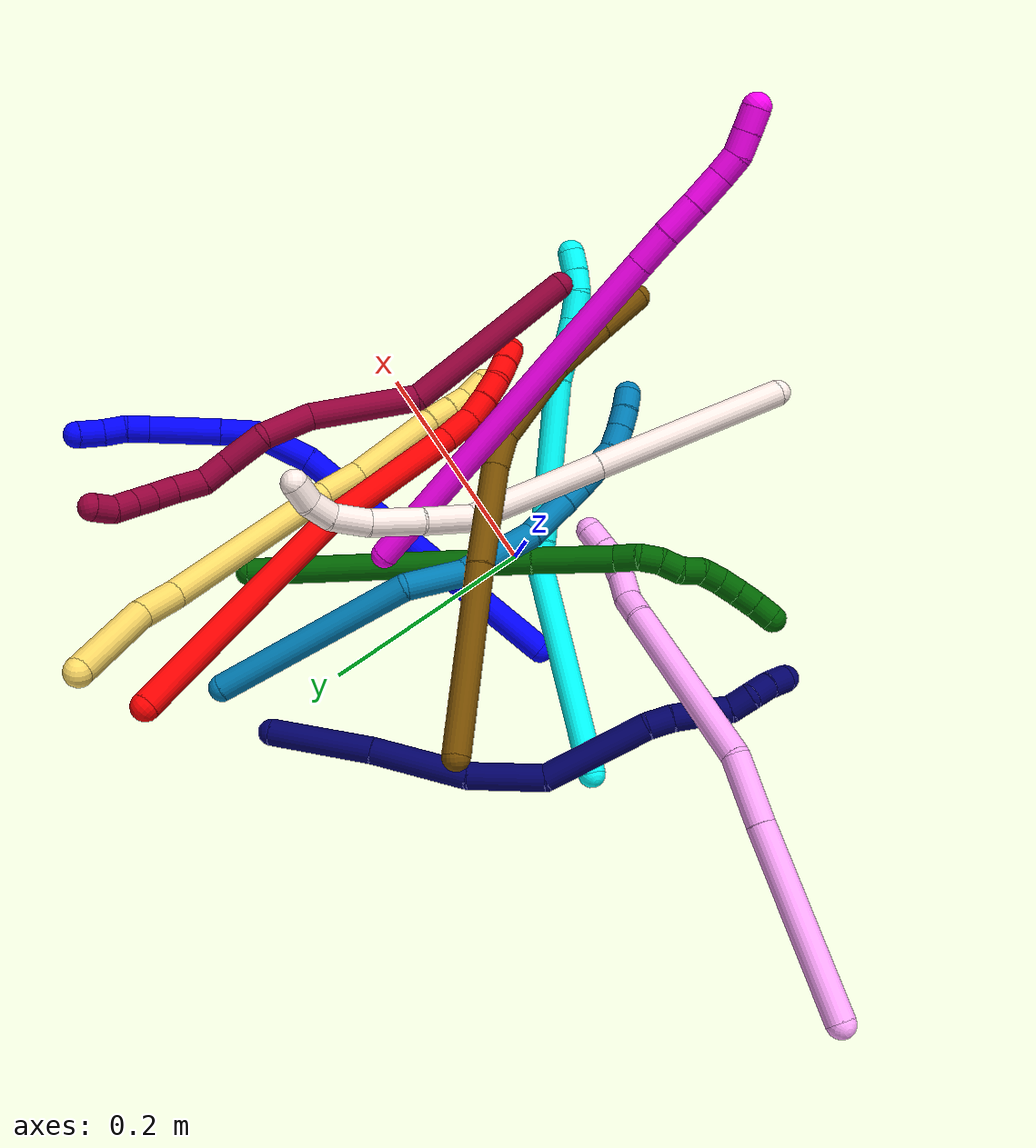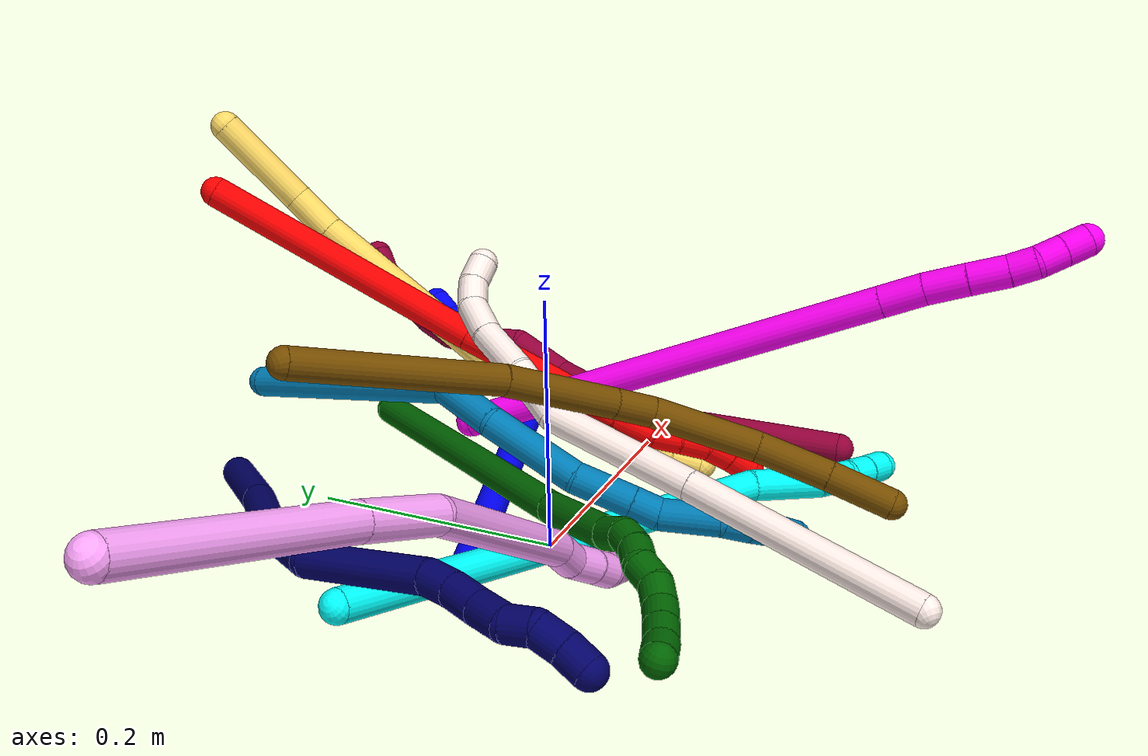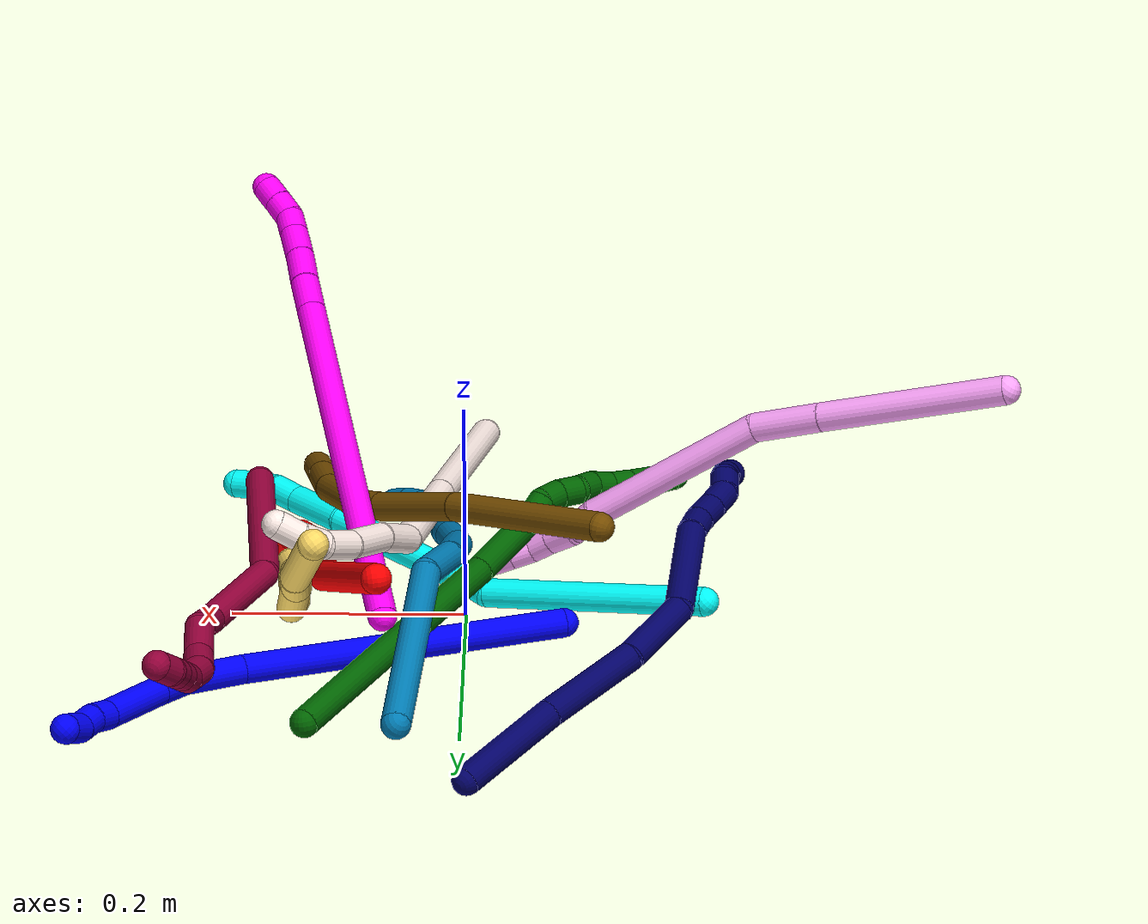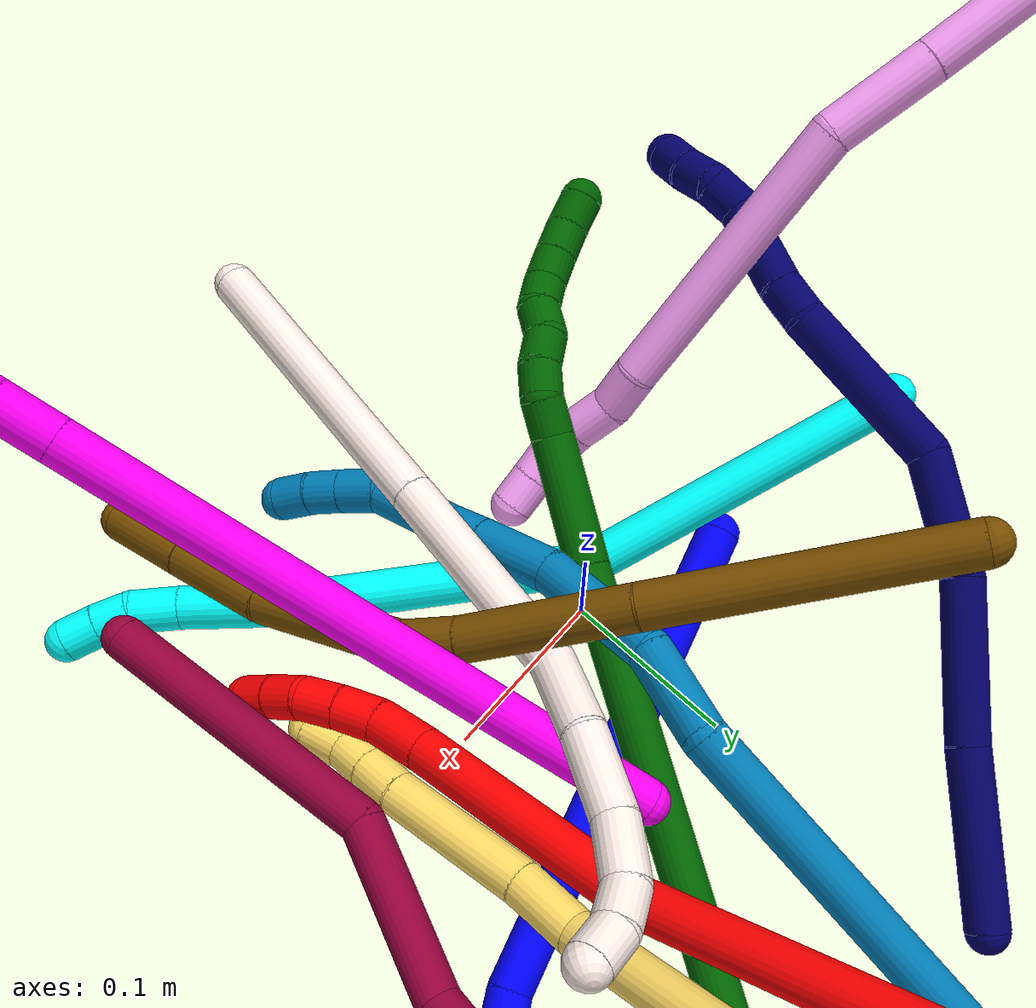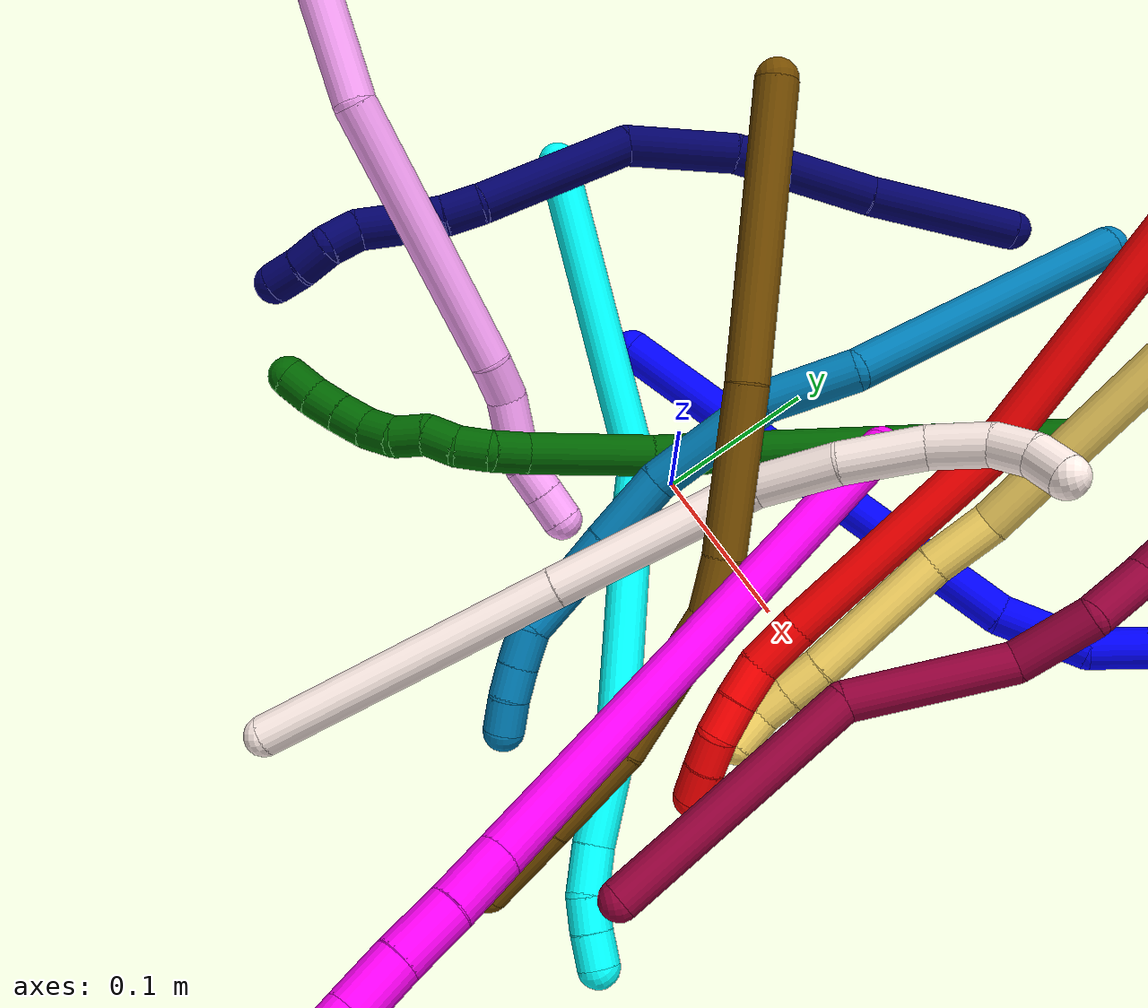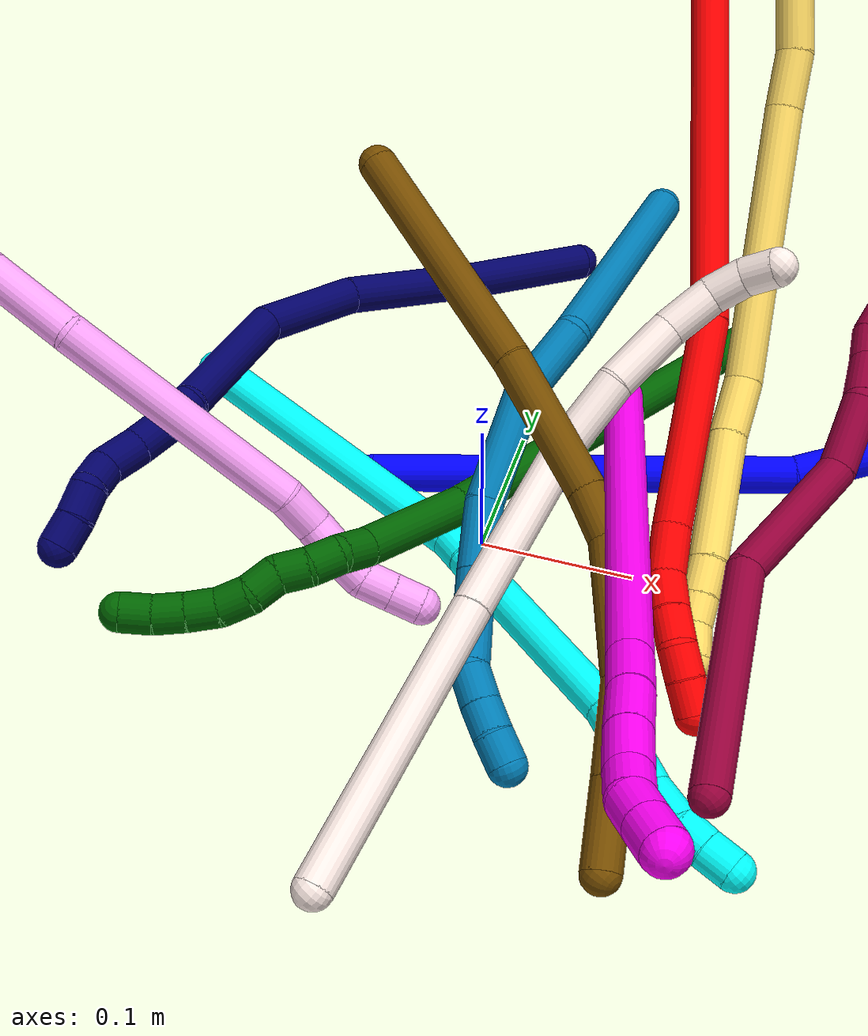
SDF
<sdf version="1.7">
 <world name="default">
  <plugin name="TubeGeneratorPlugin" filename="libtube_generator_plugin.so"/>
  <model name="photoneo_s_sensor">
   <static>1</static>
   <pose>0 0 2 1.57079 1.57079 3.14159</pose>
   <link name="link">
    <inertial><mass>0.1</mass></inertial>
    <sensor name="sensor" type="depth">
     <update_rate>30</update_rate>
     <camera>
      <horizontal_fov>1.22</horizontal_fov>
      <image><width>1920</width><height>1200</height><format>B8G8R8</format></image>
      <clip><near>0.1</near><far>4</far></clip>
      <depth_camera><output>points</output></depth_camera>
     </camera>
     <plugin name="camera_plugin" filename="libgazebo_ros_depth_camera.so">
      <baseline>0.2</baseline>
      <alwaysOn>1</alwaysOn>
      <updateRate>0.0</updateRate>
      <cameraName>camera_ir</cameraName>
      <imageTopicName>/camera/color/image_raw</imageTopicName>
      <cameraInfoTopicName>/camera/color/camera_info</cameraInfoTopicName>
      <depthImageTopicName>/camera/depth/image_raw</depthImageTopicName>
      <depthImageCameraInfoTopicName>/camera/depth/camera_info</depthImageCameraInfoTopicName>
      <pointCloudTopicName>/camera/depth/points</pointCloudTopicName>
      <frameName>fr_optical</frameName>
      <pointCloudCutoff>0.1</pointCloudCutoff>
      <pointCloudCutoffMax>2.0</pointCloudCutoffMax>
      <distortionK1>0</distortionK1>
      <distortionK2>0</distortionK2>
      <distortionK3>0</distortionK3>
      <distortionT1>0</distortionT1>
      <distortionT2>0</distortionT2>
      <CxPrime>0</CxPrime>
      <Cx>0</Cx>
      <Cy>0</Cy>
      <focalLength>0</focalLength>
      <hackBaseline>0</hackBaseline>
     </plugin>
    </sensor>
   </link>
  </model>
  <gravity>0 0 -9.8</gravity>
  <magnetic_field>6e-06 2.3e-05 -4.2e-05</magnetic_field>
  <atmosphere type="adiabatic"/>
  <physics name="default_physics" default="0" type="ode">
   <max_step_size>0.003</max_step_size>
   <real_time_factor>1</real_time_factor>
   <real_time_update_rate>1000</real_time_update_rate>
   <max_contacts>10000</max_contacts>
   <ode>
    <solver>
     <type>quick</type>
     <iters>100</iters>
     <sor>1.3</sor>
     <use_dynamic_moi_rescaling>0</use_dynamic_moi_rescaling>
    </solver>
    <constraints>
     <contact_max_correcting_vel>0</contact_max_correcting_vel>
     <contact_surface_layer>0.001</contact_surface_layer>
     <cfm>0</cfm>
     <erp>0.2</erp>
    </constraints>
   </ode>
  </physics>
  <scene><ambient>0.4 0.4 0.4 1</ambient><background>0.7 0.7 0.7 1</background><shadows>0</shadows></scene>
  <audio><device>default</device></audio>
  <spherical_coordinates>
   <surface_model>EARTH_WGS84</surface_model>
   <latitude_deg>0</latitude_deg>
   <longitude_deg>0</longitude_deg>
   <elevation>0</elevation>
   <heading_deg>0</heading_deg>
  </spherical_coordinates>
  <model name="bin">
   <static>1</static>
   <link name="bottom">
    <collision name="collision-bottom">
     <pose>0 0 -0.01 0 -0 0</pose>
     <geometry><box><size>0.8 0.6 0.02</size></box></geometry>
     <surface>
      <friction><ode><mu>100</mu><mu2>100</mu2></ode></friction>
      <contact><collide_bitmask>65535</collide_bitmask></contact>
     </surface>
    </collision>
   </link>
   <link name="west_wall">
    <collision name="collision-west_wall">
     <pose>-0.41 0 0.1 0 -0 0</pose>
     <geometry><box><size>0.02 0.6 0.2</size></box></geometry>
     <surface>
      <friction><ode><mu>100</mu><mu2>100</mu2></ode></friction>
      <contact><collide_bitmask>65535</collide_bitmask></contact>
     </surface>
    </collision>
   </link>
   <link name="east_wall">
    <collision name="collision-east_wall">
     <pose>0.41 0 0.1 0 -0 0</pose>
     <geometry><box><size>0.02 0.6 0.2</size></box></geometry>
     <surface>
      <friction><ode><mu>100</mu><mu2>100</mu2></ode></friction>
      <contact><collide_bitmask>65535</collide_bitmask></contact>
     </surface>
    </collision>
   </link>
   <link name="south_wall">
    <collision name="collision-south_wall">
     <pose>0 -0.31 0.1 0 -0 0</pose>
     <geometry><box><size>0.8 0.02 0.2</size></box></geometry>
     <surface>
      <friction><ode><mu>100</mu><mu2>100</mu2></ode></friction>
      <contact><collide_bitmask>65535</collide_bitmask></contact>
     </surface>
    </collision>
   </link>
   <link name="north_wall">
    <collision name="collision-north_wall">
     <pose>0 0.31 0.1 0 -0 0</pose>
     <geometry><box><size>0.8 0.02 0.2</size></box></geometry>
     <surface>
      <friction><ode><mu>100</mu><mu2>100</mu2></ode></friction>
      <contact><collide_bitmask>65535</collide_bitmask></contact>
     </surface>
    </collision>
   </link>
  </model>
  <model name="1">
   <static>0</static>
   <link name="1">
    <collision name="collision-cylinder-e_1_1_4">
     <pose>0.074809 0.035308 0.112748 -0.303488 0.564464 -0.088627</pose>
     <geometry><cylinder><radius>0.0125</radius><length>0.27968</length></cylinder></geometry>
     <surface>
      <friction><ode><mu>1.16</mu><mu2>1.16</mu2><slip1>0</slip1><slip2>0</slip2></ode></friction>
      <contact><ode><kp>1e+06</kp><kd>1</kd><max_vel>0</max_vel><min_depth>0.001</min_depth></ode></contact>
     </surface>
    </collision>
    <visual name="visual-cylinder-e_1_1_4">
     <pose>0.074809 0.035308 0.112748 -0.303488 0.564464 -0.088627</pose>
     <geometry><cylinder><radius>0.0125</radius><length>0.27968</length></cylinder></geometry>
     <material><ambient>0 0 1 1</ambient></material>
    </visual>
    <collision name="collision-cylinder-e_2_4_5">
     <pose>0.167174 0.071193 0.246224 -0.027811 0.702532 -0.010192</pose>
     <geometry><cylinder><radius>0.0125</radius><length>0.054339</length></cylinder></geometry>
     <surface>
      <friction><ode><mu>1.16</mu><mu2>1.16</mu2><slip1>0</slip1><slip2>0</slip2></ode></friction>
      <contact><ode><kp>1e+06</kp><kd>1</kd><max_vel>0</max_vel><min_depth>0.001</min_depth></ode></contact>
     </surface>
    </collision>
    <visual name="visual-cylinder-e_2_4_5">
     <pose>0.167174 0.071193 0.246224 -0.027811 0.702532 -0.010192</pose>
     <geometry><cylinder><radius>0.0125</radius><length>0.054339</length></cylinder></geometry>
     <material><ambient>0 0 1 1</ambient></material>
    </visual>
    <collision name="collision-cylinder-e_3_5_6">
     <pose>0.196224 0.065473 0.277846 0.524041 0.740186 0.20735</pose>
     <geometry><cylinder><radius>0.0125</radius><length>0.034086</length></cylinder></geometry>
     <surface>
      <friction><ode><mu>1.16</mu><mu2>1.16</mu2><slip1>0</slip1><slip2>0</slip2></ode></friction>
      <contact><ode><kp>1e+06</kp><kd>1</kd><max_vel>0</max_vel><min_depth>0.001</min_depth></ode></contact>
     </surface>
    </collision>
    <visual name="visual-cylinder-e_3_5_6">
     <pose>0.196224 0.065473 0.277846 0.524041 0.740186 0.20735</pose>
     <geometry><cylinder><radius>0.0125</radius><length>0.034086</length></cylinder></geometry>
     <material><ambient>0 0 1 1</ambient></material>
    </visual>
    <collision name="collision-cylinder-e_4_6_7">
     <pose>0.229285 0.046365 0.30982 0.546142 0.718435 0.209566</pose>
     <geometry><cylinder><radius>0.0125</radius><length>0.065531</length></cylinder></geometry>
     <surface>
      <friction><ode><mu>1.16</mu><mu2>1.16</mu2><slip1>0</slip1><slip2>0</slip2></ode></friction>
      <contact><ode><kp>1e+06</kp><kd>1</kd><max_vel>0</max_vel><min_depth>0.001</min_depth></ode></contact>
     </surface>
    </collision>
    <visual name="visual-cylinder-e_4_6_7">
     <pose>0.229285 0.046365 0.30982 0.546142 0.718435 0.209566</pose>
     <geometry><cylinder><radius>0.0125</radius><length>0.065531</length></cylinder></geometry>
     <material><ambient>0 0 1 1</ambient></material>
    </visual>
    <collision name="collision-cylinder-e_5_7_8">
     <pose>0.258712 0.02948 0.336156 0.659155 0.868681 0.314723</pose>
     <geometry><cylinder><radius>0.0125</radius><length>0.020591</length></cylinder></geometry>
     <surface>
      <friction><ode><mu>1.16</mu><mu2>1.16</mu2><slip1>0</slip1><slip2>0</slip2></ode></friction>
      <contact><ode><kp>1e+06</kp><kd>1</kd><max_vel>0</max_vel><min_depth>0.001</min_depth></ode></contact>
     </surface>
    </collision>
    <visual name="visual-cylinder-e_5_7_8">
     <pose>0.258712 0.02948 0.336156 0.659155 0.868681 0.314723</pose>
     <geometry><cylinder><radius>0.0125</radius><length>0.020591</length></cylinder></geometry>
     <material><ambient>0 0 1 1</ambient></material>
    </visual>
    <collision name="collision-cylinder-e_6_8_9">
     <pose>0.27296 0.019295 0.347201 0.812588 0.649066 0.287488</pose>
     <geometry><cylinder><radius>0.0125</radius><length>0.021137</length></cylinder></geometry>
     <surface>
      <friction><ode><mu>1.16</mu><mu2>1.16</mu2><slip1>0</slip1><slip2>0</slip2></ode></friction>
      <contact><ode><kp>1e+06</kp><kd>1</kd><max_vel>0</max_vel><min_depth>0.001</min_depth></ode></contact>
     </surface>
    </collision>
    <visual name="visual-cylinder-e_6_8_9">
     <pose>0.27296 0.019295 0.347201 0.812588 0.649066 0.287488</pose>
     <geometry><cylinder><radius>0.0125</radius><length>0.021137</length></cylinder></geometry>
     <material><ambient>0 0 1 1</ambient></material>
    </visual>
    <collision name="collision-cylinder-e_7_9_2">
     <pose>0.289475 0.007468 0.357057 0.952282 0.965098 0.527722</pose>
     <geometry><cylinder><radius>0.0125</radius><length>0.024636</length></cylinder></geometry>
     <surface>
      <friction><ode><mu>1.16</mu><mu2>1.16</mu2><slip1>0</slip1><slip2>0</slip2></ode></friction>
      <contact><ode><kp>1e+06</kp><kd>1</kd><max_vel>0</max_vel><min_depth>0.001</min_depth></ode></contact>
     </surface>
    </collision>
    <visual name="visual-cylinder-e_7_9_2">
     <pose>0.289475 0.007468 0.357057 0.952282 0.965098 0.527722</pose>
     <geometry><cylinder><radius>0.0125</radius><length>0.024636</length></cylinder></geometry>
     <material><ambient>0 0 1 1</ambient></material>
    </visual>
    <collision name="collision-sphere-2">
     <pose>0.299602 0.001754 0.361123 0 -0 0</pose>
     <geometry><sphere><radius>0.0125</radius></sphere></geometry>
     <surface>
      <friction><ode><mu>1.16</mu><mu2>1.16</mu2><slip1>0</slip1><slip2>0</slip2></ode></friction>
      <contact><ode><kp>1e+06</kp><kd>1</kd><max_vel>0</max_vel><min_depth>0.001</min_depth></ode></contact>
     </surface>
    </collision>
    <visual name="visual-sphere-2">
     <pose>0.299602 0.001754 0.361123 0 -0 0</pose>
     <geometry><sphere><radius>0.0125</radius></sphere></geometry>
     <material><ambient>0 0 1 1</ambient></material>
    </visual>
    <collision name="collision-sphere-9">
     <pose>0.279348 0.013182 0.35299 0 -0 0</pose>
     <geometry><sphere><radius>0.0125</radius></sphere></geometry>
     <surface>
      <friction><ode><mu>1.16</mu><mu2>1.16</mu2><slip1>0</slip1><slip2>0</slip2></ode></friction>
      <contact><ode><kp>1e+06</kp><kd>1</kd><max_vel>0</max_vel><min_depth>0.001</min_depth></ode></contact>
     </surface>
    </collision>
    <visual name="visual-sphere-9">
     <pose>0.279348 0.013182 0.35299 0 -0 0</pose>
     <geometry><sphere><radius>0.0125</radius></sphere></geometry>
     <material><ambient>0 0 1 1</ambient></material>
    </visual>
    <collision name="collision-sphere-4">
     <pose>0.149618 0.070617 0.225496 0 -0 0</pose>
     <geometry><sphere><radius>0.0125</radius></sphere></geometry>
     <surface>
      <friction><ode><mu>1.16</mu><mu2>1.16</mu2><slip1>0</slip1><slip2>0</slip2></ode></friction>
      <contact><ode><kp>1e+06</kp><kd>1</kd><max_vel>0</max_vel><min_depth>0.001</min_depth></ode></contact>
     </surface>
    </collision>
    <visual name="visual-sphere-4">
     <pose>0.149618 0.070617 0.225496 0 -0 0</pose>
     <geometry><sphere><radius>0.0125</radius></sphere></geometry>
     <material><ambient>0 0 1 1</ambient></material>
    </visual>
    <collision name="collision-sphere-1">
     <geometry><sphere><radius>0.0125</radius></sphere></geometry>
     <surface>
      <friction><ode><mu>1.16</mu><mu2>1.16</mu2><slip1>0</slip1><slip2>0</slip2></ode></friction>
      <contact><ode><kp>1e+06</kp><kd>1</kd><max_vel>0</max_vel><min_depth>0.001</min_depth></ode></contact>
     </surface>
    </collision>
    <visual name="visual-sphere-1">
     <geometry><sphere><radius>0.0125</radius></sphere></geometry>
     <material><ambient>0 0 1 1</ambient></material>
    </visual>
    <collision name="collision-sphere-8">
     <pose>0.266572 0.025408 0.341412 0 -0 0</pose>
     <geometry><sphere><radius>0.0125</radius></sphere></geometry>
     <surface>
      <friction><ode><mu>1.16</mu><mu2>1.16</mu2><slip1>0</slip1><slip2>0</slip2></ode></friction>
      <contact><ode><kp>1e+06</kp><kd>1</kd><max_vel>0</max_vel><min_depth>0.001</min_depth></ode></contact>
     </surface>
    </collision>
    <visual name="visual-sphere-8">
     <pose>0.266572 0.025408 0.341412 0 -0 0</pose>
     <geometry><sphere><radius>0.0125</radius></sphere></geometry>
     <material><ambient>0 0 1 1</ambient></material>
    </visual>
    <collision name="collision-sphere-5">
     <pose>0.184729 0.07177 0.266951 0 -0 0</pose>
     <geometry><sphere><radius>0.0125</radius></sphere></geometry>
     <surface>
      <friction><ode><mu>1.16</mu><mu2>1.16</mu2><slip1>0</slip1><slip2>0</slip2></ode></friction>
      <contact><ode><kp>1e+06</kp><kd>1</kd><max_vel>0</max_vel><min_depth>0.001</min_depth></ode></contact>
     </surface>
    </collision>
    <visual name="visual-sphere-5">
     <pose>0.184729 0.07177 0.266951 0 -0 0</pose>
     <geometry><sphere><radius>0.0125</radius></sphere></geometry>
     <material><ambient>0 0 1 1</ambient></material>
    </visual>
    <collision name="collision-sphere-6">
     <pose>0.207718 0.059177 0.288742 0 -0 0</pose>
     <geometry><sphere><radius>0.0125</radius></sphere></geometry>
     <surface>
      <friction><ode><mu>1.16</mu><mu2>1.16</mu2><slip1>0</slip1><slip2>0</slip2></ode></friction>
      <contact><ode><kp>1e+06</kp><kd>1</kd><max_vel>0</max_vel><min_depth>0.001</min_depth></ode></contact>
     </surface>
    </collision>
    <visual name="visual-sphere-6">
     <pose>0.207718 0.059177 0.288742 0 -0 0</pose>
     <geometry><sphere><radius>0.0125</radius></sphere></geometry>
     <material><ambient>0 0 1 1</ambient></material>
    </visual>
    <collision name="collision-sphere-7">
     <pose>0.250851 0.033553 0.330899 0 -0 0</pose>
     <geometry><sphere><radius>0.0125</radius></sphere></geometry>
     <surface>
      <friction><ode><mu>1.16</mu><mu2>1.16</mu2><slip1>0</slip1><slip2>0</slip2></ode></friction>
      <contact><ode><kp>1e+06</kp><kd>1</kd><max_vel>0</max_vel><min_depth>0.001</min_depth></ode></contact>
     </surface>
    </collision>
    <visual name="visual-sphere-7">
     <pose>0.250851 0.033553 0.330899 0 -0 0</pose>
     <geometry><sphere><radius>0.0125</radius></sphere></geometry>
     <material><ambient>0 0 1 1</ambient></material>
    </visual>
    <inertial>
     <pose>0.139897 0.040425 0.195487 0 -0 0</pose>
     <mass>0.5</mass>
     <inertia>
      <ixx>0.001473</ixx>
      <ixy>0</ixy>
      <ixz>0</ixz>
      <iyy>0.001686</iyy>
      <iyz>0</iyz>
      <izz>-0.001436</izz>
     </inertia>
    </inertial>
   </link>
   <pose>-0.084567 0.030231 0.011493 3.03291 -0.96611 0.634221</pose>
  </model>
  <model name="2">
   <static>0</static>
   <link name="2">
    <collision name="collision-cylinder-e_1_1_4">
     <pose>-0.00589 -0.116989 0.013215 1.45831 -0.049987 -0.04466</pose>
     <geometry><cylinder><radius>0.0125</radius><length>0.235761</length></cylinder></geometry>
     <surface>
      <friction><ode><mu>1.16</mu><mu2>1.16</mu2><slip1>0</slip1><slip2>0</slip2></ode></friction>
      <contact><ode><kp>1e+06</kp><kd>1</kd><max_vel>0</max_vel><min_depth>0.001</min_depth></ode></contact>
     </surface>
    </collision>
    <visual name="visual-cylinder-e_1_1_4">
     <pose>-0.00589 -0.116989 0.013215 1.45831 -0.049987 -0.04466</pose>
     <geometry><cylinder><radius>0.0125</radius><length>0.235761</length></cylinder></geometry>
     <material><ambient>1 0 0 1</ambient></material>
    </visual>
    <collision name="collision-cylinder-e_2_4_5">
     <pose>-0.022386 -0.304439 0.022147 1.63152 -0.149125 -0.158429</pose>
     <geometry><cylinder><radius>0.0125</radius><length>0.142766</length></cylinder></geometry>
     <surface>
      <friction><ode><mu>1.16</mu><mu2>1.16</mu2><slip1>0</slip1><slip2>0</slip2></ode></friction>
      <contact><ode><kp>1e+06</kp><kd>1</kd><max_vel>0</max_vel><min_depth>0.001</min_depth></ode></contact>
     </surface>
    </collision>
    <visual name="visual-cylinder-e_2_4_5">
     <pose>-0.022386 -0.304439 0.022147 1.63152 -0.149125 -0.158429</pose>
     <geometry><cylinder><radius>0.0125</radius><length>0.142766</length></cylinder></geometry>
     <material><ambient>1 0 0 1</ambient></material>
    </visual>
    <collision name="collision-cylinder-e_3_5_6">
     <pose>-0.03647 -0.39064 0.017631 1.58551 -0.217494 -0.220693</pose>
     <geometry><cylinder><radius>0.0125</radius><length>0.032244</length></cylinder></geometry>
     <surface>
      <friction><ode><mu>1.16</mu><mu2>1.16</mu2><slip1>0</slip1><slip2>0</slip2></ode></friction>
      <contact><ode><kp>1e+06</kp><kd>1</kd><max_vel>0</max_vel><min_depth>0.001</min_depth></ode></contact>
     </surface>
    </collision>
    <visual name="visual-cylinder-e_3_5_6">
     <pose>-0.03647 -0.39064 0.017631 1.58551 -0.217494 -0.220693</pose>
     <geometry><cylinder><radius>0.0125</radius><length>0.032244</length></cylinder></geometry>
     <material><ambient>1 0 0 1</ambient></material>
    </visual>
    <collision name="collision-cylinder-e_4_6_7">
     <pose>-0.044038 -0.417342 0.019831 1.35249 -0.349249 -0.281278</pose>
     <geometry><cylinder><radius>0.0125</radius><length>0.023898</length></cylinder></geometry>
     <surface>
      <friction><ode><mu>1.16</mu><mu2>1.16</mu2><slip1>0</slip1><slip2>0</slip2></ode></friction>
      <contact><ode><kp>1e+06</kp><kd>1</kd><max_vel>0</max_vel><min_depth>0.001</min_depth></ode></contact>
     </surface>
    </collision>
    <visual name="visual-cylinder-e_4_6_7">
     <pose>-0.044038 -0.417342 0.019831 1.35249 -0.349249 -0.281278</pose>
     <geometry><cylinder><radius>0.0125</radius><length>0.023898</length></cylinder></geometry>
     <material><ambient>1 0 0 1</ambient></material>
    </visual>
    <collision name="collision-cylinder-e_5_7_8">
     <pose>-0.051364 -0.438868 0.025343 1.28714 -0.286072 -0.215226</pose>
     <geometry><cylinder><radius>0.0125</radius><length>0.022941</length></cylinder></geometry>
     <surface>
      <friction><ode><mu>1.16</mu><mu2>1.16</mu2><slip1>0</slip1><slip2>0</slip2></ode></friction>
      <contact><ode><kp>1e+06</kp><kd>1</kd><max_vel>0</max_vel><min_depth>0.001</min_depth></ode></contact>
     </surface>
    </collision>
    <visual name="visual-cylinder-e_5_7_8">
     <pose>-0.051364 -0.438868 0.025343 1.28714 -0.286072 -0.215226</pose>
     <geometry><cylinder><radius>0.0125</radius><length>0.022941</length></cylinder></geometry>
     <material><ambient>1 0 0 1</ambient></material>
    </visual>
    <collision name="collision-cylinder-e_6_8_9">
     <pose>-0.054424 -0.459114 0.032149 1.20335 0.017048 0.011705</pose>
     <geometry><cylinder><radius>0.0125</radius><length>0.020751</length></cylinder></geometry>
     <surface>
      <friction><ode><mu>1.16</mu><mu2>1.16</mu2><slip1>0</slip1><slip2>0</slip2></ode></friction>
      <contact><ode><kp>1e+06</kp><kd>1</kd><max_vel>0</max_vel><min_depth>0.001</min_depth></ode></contact>
     </surface>
    </collision>
    <visual name="visual-cylinder-e_6_8_9">
     <pose>-0.054424 -0.459114 0.032149 1.20335 0.017048 0.011705</pose>
     <geometry><cylinder><radius>0.0125</radius><length>0.020751</length></cylinder></geometry>
     <material><ambient>1 0 0 1</ambient></material>
    </visual>
    <collision name="collision-cylinder-e_7_9_2">
     <pose>-0.053121 -0.47876 0.039938 1.18373 0.104206 0.070089</pose>
     <geometry><cylinder><radius>0.0125</radius><length>0.021639</length></cylinder></geometry>
     <surface>
      <friction><ode><mu>1.16</mu><mu2>1.16</mu2><slip1>0</slip1><slip2>0</slip2></ode></friction>
      <contact><ode><kp>1e+06</kp><kd>1</kd><max_vel>0</max_vel><min_depth>0.001</min_depth></ode></contact>
     </surface>
    </collision>
    <visual name="visual-cylinder-e_7_9_2">
     <pose>-0.053121 -0.47876 0.039938 1.18373 0.104206 0.070089</pose>
     <geometry><cylinder><radius>0.0125</radius><length>0.021639</length></cylinder></geometry>
     <material><ambient>1 0 0 1</ambient></material>
    </visual>
    <collision name="collision-sphere-2">
     <pose>-0.051996 -0.488725 0.043999 0 -0 0</pose>
     <geometry><sphere><radius>0.0125</radius></sphere></geometry>
     <surface>
      <friction><ode><mu>1.16</mu><mu2>1.16</mu2><slip1>0</slip1><slip2>0</slip2></ode></friction>
      <contact><ode><kp>1e+06</kp><kd>1</kd><max_vel>0</max_vel><min_depth>0.001</min_depth></ode></contact>
     </surface>
    </collision>
    <visual name="visual-sphere-2">
     <pose>-0.051996 -0.488725 0.043999 0 -0 0</pose>
     <geometry><sphere><radius>0.0125</radius></sphere></geometry>
     <material><ambient>1 0 0 1</ambient></material>
    </visual>
    <collision name="collision-sphere-9">
     <pose>-0.054247 -0.468795 0.035876 0 -0 0</pose>
     <geometry><sphere><radius>0.0125</radius></sphere></geometry>
     <surface>
      <friction><ode><mu>1.16</mu><mu2>1.16</mu2><slip1>0</slip1><slip2>0</slip2></ode></friction>
      <contact><ode><kp>1e+06</kp><kd>1</kd><max_vel>0</max_vel><min_depth>0.001</min_depth></ode></contact>
     </surface>
    </collision>
    <visual name="visual-sphere-9">
     <pose>-0.054247 -0.468795 0.035876 0 -0 0</pose>
     <geometry><sphere><radius>0.0125</radius></sphere></geometry>
     <material><ambient>1 0 0 1</ambient></material>
    </visual>
    <collision name="collision-sphere-4">
     <pose>-0.01178 -0.233978 0.026431 0 -0 0</pose>
     <geometry><sphere><radius>0.0125</radius></sphere></geometry>
     <surface>
      <friction><ode><mu>1.16</mu><mu2>1.16</mu2><slip1>0</slip1><slip2>0</slip2></ode></friction>
      <contact><ode><kp>1e+06</kp><kd>1</kd><max_vel>0</max_vel><min_depth>0.001</min_depth></ode></contact>
     </surface>
    </collision>
    <visual name="visual-sphere-4">
     <pose>-0.01178 -0.233978 0.026431 0 -0 0</pose>
     <geometry><sphere><radius>0.0125</radius></sphere></geometry>
     <material><ambient>1 0 0 1</ambient></material>
    </visual>
    <collision name="collision-sphere-1">
     <geometry><sphere><radius>0.0125</radius></sphere></geometry>
     <surface>
      <friction><ode><mu>1.16</mu><mu2>1.16</mu2><slip1>0</slip1><slip2>0</slip2></ode></friction>
      <contact><ode><kp>1e+06</kp><kd>1</kd><max_vel>0</max_vel><min_depth>0.001</min_depth></ode></contact>
     </surface>
    </collision>
    <visual name="visual-sphere-1">
     <geometry><sphere><radius>0.0125</radius></sphere></geometry>
     <material><ambient>1 0 0 1</ambient></material>
    </visual>
    <collision name="collision-sphere-8">
     <pose>-0.054601 -0.449433 0.028422 0 -0 0</pose>
     <geometry><sphere><radius>0.0125</radius></sphere></geometry>
     <surface>
      <friction><ode><mu>1.16</mu><mu2>1.16</mu2><slip1>0</slip1><slip2>0</slip2></ode></friction>
      <contact><ode><kp>1e+06</kp><kd>1</kd><max_vel>0</max_vel><min_depth>0.001</min_depth></ode></contact>
     </surface>
    </collision>
    <visual name="visual-sphere-8">
     <pose>-0.054601 -0.449433 0.028422 0 -0 0</pose>
     <geometry><sphere><radius>0.0125</radius></sphere></geometry>
     <material><ambient>1 0 0 1</ambient></material>
    </visual>
    <collision name="collision-sphere-5">
     <pose>-0.032991 -0.3749 0.017863 0 -0 0</pose>
     <geometry><sphere><radius>0.0125</radius></sphere></geometry>
     <surface>
      <friction><ode><mu>1.16</mu><mu2>1.16</mu2><slip1>0</slip1><slip2>0</slip2></ode></friction>
      <contact><ode><kp>1e+06</kp><kd>1</kd><max_vel>0</max_vel><min_depth>0.001</min_depth></ode></contact>
     </surface>
    </collision>
    <visual name="visual-sphere-5">
     <pose>-0.032991 -0.3749 0.017863 0 -0 0</pose>
     <geometry><sphere><radius>0.0125</radius></sphere></geometry>
     <material><ambient>1 0 0 1</ambient></material>
    </visual>
    <collision name="collision-sphere-6">
     <pose>-0.039949 -0.406381 0.0174 0 -0 0</pose>
     <geometry><sphere><radius>0.0125</radius></sphere></geometry>
     <surface>
      <friction><ode><mu>1.16</mu><mu2>1.16</mu2><slip1>0</slip1><slip2>0</slip2></ode></friction>
      <contact><ode><kp>1e+06</kp><kd>1</kd><max_vel>0</max_vel><min_depth>0.001</min_depth></ode></contact>
     </surface>
    </collision>
    <visual name="visual-sphere-6">
     <pose>-0.039949 -0.406381 0.0174 0 -0 0</pose>
     <geometry><sphere><radius>0.0125</radius></sphere></geometry>
     <material><ambient>1 0 0 1</ambient></material>
    </visual>
    <collision name="collision-sphere-7">
     <pose>-0.048127 -0.428303 0.022263 0 -0 0</pose>
     <geometry><sphere><radius>0.0125</radius></sphere></geometry>
     <surface>
      <friction><ode><mu>1.16</mu><mu2>1.16</mu2><slip1>0</slip1><slip2>0</slip2></ode></friction>
      <contact><ode><kp>1e+06</kp><kd>1</kd><max_vel>0</max_vel><min_depth>0.001</min_depth></ode></contact>
     </surface>
    </collision>
    <visual name="visual-sphere-7">
     <pose>-0.048127 -0.428303 0.022263 0 -0 0</pose>
     <geometry><sphere><radius>0.0125</radius></sphere></geometry>
     <material><ambient>1 0 0 1</ambient></material>
    </visual>
    <inertial>
     <pose>-0.02054 -0.247139 0.018865 0 -0 0</pose>
     <mass>0.5</mass>
     <inertia><ixx>0.001258</ixx><ixy>0</ixy><ixz>0</ixz><iyy>-8e-06</iyy><iyz>0</iyz><izz>0.001446</izz></inertia>
    </inertial>
   </link>
   <pose>0.058996 0.325946 0.228354 1.6782 1.01013 1.82916</pose>
  </model>
  <model name="3">
   <static>0</static>
   <link name="3">
    <collision name="collision-cylinder-e_1_1_4">
     <pose>0.059411 -0.015371 -0.079628 2.95091 0.632266 2.57272</pose>
     <geometry><cylinder><radius>0.0125</radius><length>0.201062</length></cylinder></geometry>
     <surface>
      <friction><ode><mu>1.16</mu><mu2>1.16</mu2><slip1>0</slip1><slip2>0</slip2></ode></friction>
      <contact><ode><kp>1e+06</kp><kd>1</kd><max_vel>0</max_vel><min_depth>0.001</min_depth></ode></contact>
     </surface>
    </collision>
    <visual name="visual-cylinder-e_1_1_4">
     <pose>0.059411 -0.015371 -0.079628 2.95091 0.632266 2.57272</pose>
     <geometry><cylinder><radius>0.0125</radius><length>0.201062</length></cylinder></geometry>
     <material><ambient>0.003922 1 0.996078 1</ambient></material>
    </visual>
    <collision name="collision-cylinder-e_2_4_5">
     <pose>0.126942 -0.035798 -0.164574 2.38148 0.835872 1.67648</pose>
     <geometry><cylinder><radius>0.0125</radius><length>0.021889</length></cylinder></geometry>
     <surface>
      <friction><ode><mu>1.16</mu><mu2>1.16</mu2><slip1>0</slip1><slip2>0</slip2></ode></friction>
      <contact><ode><kp>1e+06</kp><kd>1</kd><max_vel>0</max_vel><min_depth>0.001</min_depth></ode></contact>
     </surface>
    </collision>
    <visual name="visual-cylinder-e_2_4_5">
     <pose>0.126942 -0.035798 -0.164574 2.38148 0.835872 1.67648</pose>
     <geometry><cylinder><radius>0.0125</radius><length>0.021889</length></cylinder></geometry>
     <material><ambient>0.003922 1 0.996078 1</ambient></material>
    </visual>
    <collision name="collision-cylinder-e_3_5_6">
     <pose>0.188272 -0.073023 -0.210986 2.47742 0.795104 1.76644</pose>
     <geometry><cylinder><radius>0.0125</radius><length>0.149062</length></cylinder></geometry>
     <surface>
      <friction><ode><mu>1.16</mu><mu2>1.16</mu2><slip1>0</slip1><slip2>0</slip2></ode></friction>
      <contact><ode><kp>1e+06</kp><kd>1</kd><max_vel>0</max_vel><min_depth>0.001</min_depth></ode></contact>
     </surface>
    </collision>
    <visual name="visual-cylinder-e_3_5_6">
     <pose>0.188272 -0.073023 -0.210986 2.47742 0.795104 1.76644</pose>
     <geometry><cylinder><radius>0.0125</radius><length>0.149062</length></cylinder></geometry>
     <material><ambient>0.003922 1 0.996078 1</ambient></material>
    </visual>
    <collision name="collision-cylinder-e_4_6_7">
     <pose>0.258194 -0.122635 -0.269803 2.36416 0.591716 1.2796</pose>
     <geometry><cylinder><radius>0.0125</radius><length>0.05992</length></cylinder></geometry>
     <surface>
      <friction><ode><mu>1.16</mu><mu2>1.16</mu2><slip1>0</slip1><slip2>0</slip2></ode></friction>
      <contact><ode><kp>1e+06</kp><kd>1</kd><max_vel>0</max_vel><min_depth>0.001</min_depth></ode></contact>
     </surface>
    </collision>
    <visual name="visual-cylinder-e_4_6_7">
     <pose>0.258194 -0.122635 -0.269803 2.36416 0.591716 1.2796</pose>
     <geometry><cylinder><radius>0.0125</radius><length>0.05992</length></cylinder></geometry>
     <material><ambient>0.003922 1 0.996078 1</ambient></material>
    </visual>
    <collision name="collision-cylinder-e_5_7_8">
     <pose>0.284411 -0.146877 -0.295197 2.41637 0.747684 1.60423</pose>
     <geometry><cylinder><radius>0.0125</radius><length>0.02796</length></cylinder></geometry>
     <surface>
      <friction><ode><mu>1.16</mu><mu2>1.16</mu2><slip1>0</slip1><slip2>0</slip2></ode></friction>
      <contact><ode><kp>1e+06</kp><kd>1</kd><max_vel>0</max_vel><min_depth>0.001</min_depth></ode></contact>
     </surface>
    </collision>
    <visual name="visual-cylinder-e_5_7_8">
     <pose>0.284411 -0.146877 -0.295197 2.41637 0.747684 1.60423</pose>
     <geometry><cylinder><radius>0.0125</radius><length>0.02796</length></cylinder></geometry>
     <material><ambient>0.003922 1 0.996078 1</ambient></material>
    </visual>
    <collision name="collision-cylinder-e_6_8_9">
     <pose>0.300252 -0.156388 -0.310168 2.78582 0.683001 2.20499</pose>
     <geometry><cylinder><radius>0.0125</radius><length>0.020077</length></cylinder></geometry>
     <surface>
      <friction><ode><mu>1.16</mu><mu2>1.16</mu2><slip1>0</slip1><slip2>0</slip2></ode></friction>
      <contact><ode><kp>1e+06</kp><kd>1</kd><max_vel>0</max_vel><min_depth>0.001</min_depth></ode></contact>
     </surface>
    </collision>
    <visual name="visual-cylinder-e_6_8_9">
     <pose>0.300252 -0.156388 -0.310168 2.78582 0.683001 2.20499</pose>
     <geometry><cylinder><radius>0.0125</radius><length>0.020077</length></cylinder></geometry>
     <material><ambient>0.003922 1 0.996078 1</ambient></material>
    </visual>
    <collision name="collision-cylinder-e_7_9_2">
     <pose>0.312836 -0.161018 -0.325054 2.89405 0.673788 2.45901</pose>
     <geometry><cylinder><radius>0.0125</radius><length>0.020029</length></cylinder></geometry>
     <surface>
      <friction><ode><mu>1.16</mu><mu2>1.16</mu2><slip1>0</slip1><slip2>0</slip2></ode></friction>
      <contact><ode><kp>1e+06</kp><kd>1</kd><max_vel>0</max_vel><min_depth>0.001</min_depth></ode></contact>
     </surface>
    </collision>
    <visual name="visual-cylinder-e_7_9_2">
     <pose>0.312836 -0.161018 -0.325054 2.89405 0.673788 2.45901</pose>
     <geometry><cylinder><radius>0.0125</radius><length>0.020029</length></cylinder></geometry>
     <material><ambient>0.003922 1 0.996078 1</ambient></material>
    </visual>
    <collision name="collision-sphere-2">
     <pose>0.319085 -0.162936 -0.332642 0 -0 0</pose>
     <geometry><sphere><radius>0.0125</radius></sphere></geometry>
     <surface>
      <friction><ode><mu>1.16</mu><mu2>1.16</mu2><slip1>0</slip1><slip2>0</slip2></ode></friction>
      <contact><ode><kp>1e+06</kp><kd>1</kd><max_vel>0</max_vel><min_depth>0.001</min_depth></ode></contact>
     </surface>
    </collision>
    <visual name="visual-sphere-2">
     <pose>0.319085 -0.162936 -0.332642 0 -0 0</pose>
     <geometry><sphere><radius>0.0125</radius></sphere></geometry>
     <material><ambient>0.003922 1 0.996078 1</ambient></material>
    </visual>
    <collision name="collision-sphere-9">
     <pose>0.306588 -0.159101 -0.317467 0 -0 0</pose>
     <geometry><sphere><radius>0.0125</radius></sphere></geometry>
     <surface>
      <friction><ode><mu>1.16</mu><mu2>1.16</mu2><slip1>0</slip1><slip2>0</slip2></ode></friction>
      <contact><ode><kp>1e+06</kp><kd>1</kd><max_vel>0</max_vel><min_depth>0.001</min_depth></ode></contact>
     </surface>
    </collision>
    <visual name="visual-sphere-9">
     <pose>0.306588 -0.159101 -0.317467 0 -0 0</pose>
     <geometry><sphere><radius>0.0125</radius></sphere></geometry>
     <material><ambient>0.003922 1 0.996078 1</ambient></material>
    </visual>
    <collision name="collision-sphere-4">
     <pose>0.118823 -0.030741 -0.159255 0 -0 0</pose>
     <geometry><sphere><radius>0.0125</radius></sphere></geometry>
     <surface>
      <friction><ode><mu>1.16</mu><mu2>1.16</mu2><slip1>0</slip1><slip2>0</slip2></ode></friction>
      <contact><ode><kp>1e+06</kp><kd>1</kd><max_vel>0</max_vel><min_depth>0.001</min_depth></ode></contact>
     </surface>
    </collision>
    <visual name="visual-sphere-4">
     <pose>0.118823 -0.030741 -0.159255 0 -0 0</pose>
     <geometry><sphere><radius>0.0125</radius></sphere></geometry>
     <material><ambient>0.003922 1 0.996078 1</ambient></material>
    </visual>
    <collision name="collision-sphere-1">
     <geometry><sphere><radius>0.0125</radius></sphere></geometry>
     <surface>
      <friction><ode><mu>1.16</mu><mu2>1.16</mu2><slip1>0</slip1><slip2>0</slip2></ode></friction>
      <contact><ode><kp>1e+06</kp><kd>1</kd><max_vel>0</max_vel><min_depth>0.001</min_depth></ode></contact>
     </surface>
    </collision>
    <visual name="visual-sphere-1">
     <geometry><sphere><radius>0.0125</radius></sphere></geometry>
     <material><ambient>0.003922 1 0.996078 1</ambient></material>
    </visual>
    <collision name="collision-sphere-8">
     <pose>0.293916 -0.153676 -0.302868 0 -0 0</pose>
     <geometry><sphere><radius>0.0125</radius></sphere></geometry>
     <surface>
      <friction><ode><mu>1.16</mu><mu2>1.16</mu2><slip1>0</slip1><slip2>0</slip2></ode></friction>
      <contact><ode><kp>1e+06</kp><kd>1</kd><max_vel>0</max_vel><min_depth>0.001</min_depth></ode></contact>
     </surface>
    </collision>
    <visual name="visual-sphere-8">
     <pose>0.293916 -0.153676 -0.302868 0 -0 0</pose>
     <geometry><sphere><radius>0.0125</radius></sphere></geometry>
     <material><ambient>0.003922 1 0.996078 1</ambient></material>
    </visual>
    <collision name="collision-sphere-5">
     <pose>0.135062 -0.040854 -0.169892 0 -0 0</pose>
     <geometry><sphere><radius>0.0125</radius></sphere></geometry>
     <surface>
      <friction><ode><mu>1.16</mu><mu2>1.16</mu2><slip1>0</slip1><slip2>0</slip2></ode></friction>
      <contact><ode><kp>1e+06</kp><kd>1</kd><max_vel>0</max_vel><min_depth>0.001</min_depth></ode></contact>
     </surface>
    </collision>
    <visual name="visual-sphere-5">
     <pose>0.135062 -0.040854 -0.169892 0 -0 0</pose>
     <geometry><sphere><radius>0.0125</radius></sphere></geometry>
     <material><ambient>0.003922 1 0.996078 1</ambient></material>
    </visual>
    <collision name="collision-sphere-6">
     <pose>0.241483 -0.105192 -0.25208 0 -0 0</pose>
     <geometry><sphere><radius>0.0125</radius></sphere></geometry>
     <surface>
      <friction><ode><mu>1.16</mu><mu2>1.16</mu2><slip1>0</slip1><slip2>0</slip2></ode></friction>
      <contact><ode><kp>1e+06</kp><kd>1</kd><max_vel>0</max_vel><min_depth>0.001</min_depth></ode></contact>
     </surface>
    </collision>
    <visual name="visual-sphere-6">
     <pose>0.241483 -0.105192 -0.25208 0 -0 0</pose>
     <geometry><sphere><radius>0.0125</radius></sphere></geometry>
     <material><ambient>0.003922 1 0.996078 1</ambient></material>
    </visual>
    <collision name="collision-sphere-7">
     <pose>0.274905 -0.140077 -0.287526 0 -0 0</pose>
     <geometry><sphere><radius>0.0125</radius></sphere></geometry>
     <surface>
      <friction><ode><mu>1.16</mu><mu2>1.16</mu2><slip1>0</slip1><slip2>0</slip2></ode></friction>
      <contact><ode><kp>1e+06</kp><kd>1</kd><max_vel>0</max_vel><min_depth>0.001</min_depth></ode></contact>
     </surface>
    </collision>
    <visual name="visual-sphere-7">
     <pose>0.274905 -0.140077 -0.287526 0 -0 0</pose>
     <geometry><sphere><radius>0.0125</radius></sphere></geometry>
     <material><ambient>0.003922 1 0.996078 1</ambient></material>
    </visual>
    <inertial>
     <pose>0.157011 -0.065158 -0.176441 0 -0 0</pose>
     <mass>0.5</mass>
     <inertia>
      <ixx>3.6e-05</ixx>
      <ixy>0</ixy>
      <ixz>0</ixz>
      <iyy>0.001281</iyy>
      <iyz>0</iyz>
      <izz>-0.000407</izz>
     </inertia>
    </inertial>
   </link>
   <pose>-0.20274 0.056624 0.04923 0.189311 -0.763369 -0.364606</pose>
  </model>
  <model name="4">
   <static>0</static>
   <link name="4">
    <collision name="collision-cylinder-e_1_1_4">
     <pose>0.056367 -0.003234 -0.059994 3.08774 0.753507 3.00567</pose>
     <geometry><cylinder><radius>0.0125</radius><length>0.164766</length></cylinder></geometry>
     <surface>
      <friction><ode><mu>1.16</mu><mu2>1.16</mu2><slip1>0</slip1><slip2>0</slip2></ode></friction>
      <contact><ode><kp>1e+06</kp><kd>1</kd><max_vel>0</max_vel><min_depth>0.001</min_depth></ode></contact>
     </surface>
    </collision>
    <visual name="visual-cylinder-e_1_1_4">
     <pose>0.056367 -0.003234 -0.059994 3.08774 0.753507 3.00567</pose>
     <geometry><cylinder><radius>0.0125</radius><length>0.164766</length></cylinder></geometry>
     <material><ambient>1 0.65098 0.996078 1</ambient></material>
    </visual>
    <collision name="collision-cylinder-e_2_4_5">
     <pose>0.133162 -0.008775 -0.14252 3.03952 0.73389 2.87735</pose>
     <geometry><cylinder><radius>0.0125</radius><length>0.061002</length></cylinder></geometry>
     <surface>
      <friction><ode><mu>1.16</mu><mu2>1.16</mu2><slip1>0</slip1><slip2>0</slip2></ode></friction>
      <contact><ode><kp>1e+06</kp><kd>1</kd><max_vel>0</max_vel><min_depth>0.001</min_depth></ode></contact>
     </surface>
    </collision>
    <visual name="visual-cylinder-e_2_4_5">
     <pose>0.133162 -0.008775 -0.14252 3.03952 0.73389 2.87735</pose>
     <geometry><cylinder><radius>0.0125</radius><length>0.061002</length></cylinder></geometry>
     <material><ambient>1 0.65098 0.996078 1</ambient></material>
    </visual>
    <collision name="collision-cylinder-e_3_5_6">
     <pose>0.187952 -0.00769 -0.239325 -3.09594 0.432912 -2.93471</pose>
     <geometry><cylinder><radius>0.0125</radius><length>0.163814</length></cylinder></geometry>
     <surface>
      <friction><ode><mu>1.16</mu><mu2>1.16</mu2><slip1>0</slip1><slip2>0</slip2></ode></friction>
      <contact><ode><kp>1e+06</kp><kd>1</kd><max_vel>0</max_vel><min_depth>0.001</min_depth></ode></contact>
     </surface>
    </collision>
    <visual name="visual-cylinder-e_3_5_6">
     <pose>0.187952 -0.00769 -0.239325 -3.09594 0.432912 -2.93471</pose>
     <geometry><cylinder><radius>0.0125</radius><length>0.163814</length></cylinder></geometry>
     <material><ambient>1 0.65098 0.996078 1</ambient></material>
    </visual>
    <collision name="collision-cylinder-e_4_6_7">
     <pose>0.225338 -0.004996 -0.326036 3.08547 0.238221 2.68083</pose>
     <geometry><cylinder><radius>0.0125</radius><length>0.025638</length></cylinder></geometry>
     <surface>
      <friction><ode><mu>1.16</mu><mu2>1.16</mu2><slip1>0</slip1><slip2>0</slip2></ode></friction>
      <contact><ode><kp>1e+06</kp><kd>1</kd><max_vel>0</max_vel><min_depth>0.001</min_depth></ode></contact>
     </surface>
    </collision>
    <visual name="visual-cylinder-e_4_6_7">
     <pose>0.225338 -0.004996 -0.326036 3.08547 0.238221 2.68083</pose>
     <geometry><cylinder><radius>0.0125</radius><length>0.025638</length></cylinder></geometry>
     <material><ambient>1 0.65098 0.996078 1</ambient></material>
    </visual>
    <collision name="collision-cylinder-e_5_7_8">
     <pose>0.234444 -0.008291 -0.348838 2.8962 0.517473 2.26957</pose>
     <geometry><cylinder><radius>0.0125</radius><length>0.024588</length></cylinder></geometry>
     <surface>
      <friction><ode><mu>1.16</mu><mu2>1.16</mu2><slip1>0</slip1><slip2>0</slip2></ode></friction>
      <contact><ode><kp>1e+06</kp><kd>1</kd><max_vel>0</max_vel><min_depth>0.001</min_depth></ode></contact>
     </surface>
    </collision>
    <visual name="visual-cylinder-e_5_7_8">
     <pose>0.234444 -0.008291 -0.348838 2.8962 0.517473 2.26957</pose>
     <geometry><cylinder><radius>0.0125</radius><length>0.024588</length></cylinder></geometry>
     <material><ambient>1 0.65098 0.996078 1</ambient></material>
    </visual>
    <collision name="collision-cylinder-e_6_8_9">
     <pose>0.245084 -0.012148 -0.36807 3.00022 0.470699 2.56736</pose>
     <geometry><cylinder><radius>0.0125</radius><length>0.0201</length></cylinder></geometry>
     <surface>
      <friction><ode><mu>1.16</mu><mu2>1.16</mu2><slip1>0</slip1><slip2>0</slip2></ode></friction>
      <contact><ode><kp>1e+06</kp><kd>1</kd><max_vel>0</max_vel><min_depth>0.001</min_depth></ode></contact>
     </surface>
    </collision>
    <visual name="visual-cylinder-e_6_8_9">
     <pose>0.245084 -0.012148 -0.36807 3.00022 0.470699 2.56736</pose>
     <geometry><cylinder><radius>0.0125</radius><length>0.0201</length></cylinder></geometry>
     <material><ambient>1 0.65098 0.996078 1</ambient></material>
    </visual>
    <collision name="collision-cylinder-e_7_9_10">
     <pose>0.255269 -0.011266 -0.384927 -2.87941 0.597352 -2.33238</pose>
     <geometry><cylinder><radius>0.0125</radius><length>0.020009</length></cylinder></geometry>
     <surface>
      <friction><ode><mu>1.16</mu><mu2>1.16</mu2><slip1>0</slip1><slip2>0</slip2></ode></friction>
      <contact><ode><kp>1e+06</kp><kd>1</kd><max_vel>0</max_vel><min_depth>0.001</min_depth></ode></contact>
     </surface>
    </collision>
    <visual name="visual-cylinder-e_7_9_10">
     <pose>0.255269 -0.011266 -0.384927 -2.87941 0.597352 -2.33238</pose>
     <geometry><cylinder><radius>0.0125</radius><length>0.020009</length></cylinder></geometry>
     <material><ambient>1 0.65098 0.996078 1</ambient></material>
    </visual>
    <collision name="collision-cylinder-e_8_10_2">
     <pose>0.266652 -0.007028 -0.400873 -2.88424 0.610454 -2.36225</pose>
     <geometry><cylinder><radius>0.0125</radius><length>0.020083</length></cylinder></geometry>
     <surface>
      <friction><ode><mu>1.16</mu><mu2>1.16</mu2><slip1>0</slip1><slip2>0</slip2></ode></friction>
      <contact><ode><kp>1e+06</kp><kd>1</kd><max_vel>0</max_vel><min_depth>0.001</min_depth></ode></contact>
     </surface>
    </collision>
    <visual name="visual-cylinder-e_8_10_2">
     <pose>0.266652 -0.007028 -0.400873 -2.88424 0.610454 -2.36225</pose>
     <geometry><cylinder><radius>0.0125</radius><length>0.020083</length></cylinder></geometry>
     <material><ambient>1 0.65098 0.996078 1</ambient></material>
    </visual>
    <collision name="collision-sphere-2">
     <pose>0.272408 -0.004934 -0.40883 0 -0 0</pose>
     <geometry><sphere><radius>0.0125</radius></sphere></geometry>
     <surface>
      <friction><ode><mu>1.16</mu><mu2>1.16</mu2><slip1>0</slip1><slip2>0</slip2></ode></friction>
      <contact><ode><kp>1e+06</kp><kd>1</kd><max_vel>0</max_vel><min_depth>0.001</min_depth></ode></contact>
     </surface>
    </collision>
    <visual name="visual-sphere-2">
     <pose>0.272408 -0.004934 -0.40883 0 -0 0</pose>
     <geometry><sphere><radius>0.0125</radius></sphere></geometry>
     <material><ambient>1 0.65098 0.996078 1</ambient></material>
    </visual>
    <collision name="collision-sphere-10">
     <pose>0.260896 -0.009122 -0.392916 0 -0 0</pose>
     <geometry><sphere><radius>0.0125</radius></sphere></geometry>
     <surface>
      <friction><ode><mu>1.16</mu><mu2>1.16</mu2><slip1>0</slip1><slip2>0</slip2></ode></friction>
      <contact><ode><kp>1e+06</kp><kd>1</kd><max_vel>0</max_vel><min_depth>0.001</min_depth></ode></contact>
     </surface>
    </collision>
    <visual name="visual-sphere-10">
     <pose>0.260896 -0.009122 -0.392916 0 -0 0</pose>
     <geometry><sphere><radius>0.0125</radius></sphere></geometry>
     <material><ambient>1 0.65098 0.996078 1</ambient></material>
    </visual>
    <collision name="collision-sphere-9">
     <pose>0.249642 -0.01341 -0.376937 0 -0 0</pose>
     <geometry><sphere><radius>0.0125</radius></sphere></geometry>
     <surface>
      <friction><ode><mu>1.16</mu><mu2>1.16</mu2><slip1>0</slip1><slip2>0</slip2></ode></friction>
      <contact><ode><kp>1e+06</kp><kd>1</kd><max_vel>0</max_vel><min_depth>0.001</min_depth></ode></contact>
     </surface>
    </collision>
    <visual name="visual-sphere-9">
     <pose>0.249642 -0.01341 -0.376937 0 -0 0</pose>
     <geometry><sphere><radius>0.0125</radius></sphere></geometry>
     <material><ambient>1 0.65098 0.996078 1</ambient></material>
    </visual>
    <collision name="collision-sphere-4">
     <pose>0.112733 -0.006468 -0.119989 0 -0 0</pose>
     <geometry><sphere><radius>0.0125</radius></sphere></geometry>
     <surface>
      <friction><ode><mu>1.16</mu><mu2>1.16</mu2><slip1>0</slip1><slip2>0</slip2></ode></friction>
      <contact><ode><kp>1e+06</kp><kd>1</kd><max_vel>0</max_vel><min_depth>0.001</min_depth></ode></contact>
     </surface>
    </collision>
    <visual name="visual-sphere-4">
     <pose>0.112733 -0.006468 -0.119989 0 -0 0</pose>
     <geometry><sphere><radius>0.0125</radius></sphere></geometry>
     <material><ambient>1 0.65098 0.996078 1</ambient></material>
    </visual>
    <collision name="collision-sphere-1">
     <geometry><sphere><radius>0.0125</radius></sphere></geometry>
     <surface>
      <friction><ode><mu>1.16</mu><mu2>1.16</mu2><slip1>0</slip1><slip2>0</slip2></ode></friction>
      <contact><ode><kp>1e+06</kp><kd>1</kd><max_vel>0</max_vel><min_depth>0.001</min_depth></ode></contact>
     </surface>
    </collision>
    <visual name="visual-sphere-1">
     <geometry><sphere><radius>0.0125</radius></sphere></geometry>
     <material><ambient>1 0.65098 0.996078 1</ambient></material>
    </visual>
    <collision name="collision-sphere-8">
     <pose>0.240526 -0.010886 -0.359202 0 -0 0</pose>
     <geometry><sphere><radius>0.0125</radius></sphere></geometry>
     <surface>
      <friction><ode><mu>1.16</mu><mu2>1.16</mu2><slip1>0</slip1><slip2>0</slip2></ode></friction>
      <contact><ode><kp>1e+06</kp><kd>1</kd><max_vel>0</max_vel><min_depth>0.001</min_depth></ode></contact>
     </surface>
    </collision>
    <visual name="visual-sphere-8">
     <pose>0.240526 -0.010886 -0.359202 0 -0 0</pose>
     <geometry><sphere><radius>0.0125</radius></sphere></geometry>
     <material><ambient>1 0.65098 0.996078 1</ambient></material>
    </visual>
    <collision name="collision-sphere-5">
     <pose>0.15359 -0.011083 -0.165052 0 -0 0</pose>
     <geometry><sphere><radius>0.0125</radius></sphere></geometry>
     <surface>
      <friction><ode><mu>1.16</mu><mu2>1.16</mu2><slip1>0</slip1><slip2>0</slip2></ode></friction>
      <contact><ode><kp>1e+06</kp><kd>1</kd><max_vel>0</max_vel><min_depth>0.001</min_depth></ode></contact>
     </surface>
    </collision>
    <visual name="visual-sphere-5">
     <pose>0.15359 -0.011083 -0.165052 0 -0 0</pose>
     <geometry><sphere><radius>0.0125</radius></sphere></geometry>
     <material><ambient>1 0.65098 0.996078 1</ambient></material>
    </visual>
    <collision name="collision-sphere-6">
     <pose>0.222313 -0.004297 -0.313599 0 -0 0</pose>
     <geometry><sphere><radius>0.0125</radius></sphere></geometry>
     <surface>
      <friction><ode><mu>1.16</mu><mu2>1.16</mu2><slip1>0</slip1><slip2>0</slip2></ode></friction>
      <contact><ode><kp>1e+06</kp><kd>1</kd><max_vel>0</max_vel><min_depth>0.001</min_depth></ode></contact>
     </surface>
    </collision>
    <visual name="visual-sphere-6">
     <pose>0.222313 -0.004297 -0.313599 0 -0 0</pose>
     <geometry><sphere><radius>0.0125</radius></sphere></geometry>
     <material><ambient>1 0.65098 0.996078 1</ambient></material>
    </visual>
    <collision name="collision-sphere-7">
     <pose>0.228363 -0.005695 -0.338474 0 -0 0</pose>
     <geometry><sphere><radius>0.0125</radius></sphere></geometry>
     <surface>
      <friction><ode><mu>1.16</mu><mu2>1.16</mu2><slip1>0</slip1><slip2>0</slip2></ode></friction>
      <contact><ode><kp>1e+06</kp><kd>1</kd><max_vel>0</max_vel><min_depth>0.001</min_depth></ode></contact>
     </surface>
    </collision>
    <visual name="visual-sphere-7">
     <pose>0.228363 -0.005695 -0.338474 0 -0 0</pose>
     <geometry><sphere><radius>0.0125</radius></sphere></geometry>
     <material><ambient>1 0.65098 0.996078 1</ambient></material>
    </visual>
    <inertial>
     <pose>0.15026 -0.006541 -0.195742 0 -0 0</pose>
     <mass>0.5</mass>
     <inertia>
      <ixx>-0.000632</ixx>
      <ixy>0</ixy>
      <ixz>0</ixz>
      <iyy>0.000744</iyy>
      <iyz>0</iyz>
      <izz>-0.000465</izz>
     </inertia>
    </inertial>
   </link>
   <pose>-0.451495 0.01076 0.229094 0.298833 -0.49051 -0.451637</pose>
  </model>
  <model name="5">
   <static>0</static>
   <link name="5">
    <collision name="collision-cylinder-e_1_1_4">
     <pose>0.003354 -0.041483 -0.000831 1.59082 0.080664 0.082294</pose>
     <geometry><cylinder><radius>0.0125</radius><length>0.083254</length></cylinder></geometry>
     <surface>
      <friction><ode><mu>1.16</mu><mu2>1.16</mu2><slip1>0</slip1><slip2>0</slip2></ode></friction>
      <contact><ode><kp>1e+06</kp><kd>1</kd><max_vel>0</max_vel><min_depth>0.001</min_depth></ode></contact>
     </surface>
    </collision>
    <visual name="visual-cylinder-e_1_1_4">
     <pose>0.003354 -0.041483 -0.000831 1.59082 0.080664 0.082294</pose>
     <geometry><cylinder><radius>0.0125</radius><length>0.083254</length></cylinder></geometry>
     <material><ambient>1 0.858824 0.4 1</ambient></material>
    </visual>
    <collision name="collision-cylinder-e_2_4_5">
     <pose>0.012533 -0.101236 -0.001806 1.57869 0.308611 0.311019</pose>
     <geometry><cylinder><radius>0.0125</radius><length>0.038351</length></cylinder></geometry>
     <surface>
      <friction><ode><mu>1.16</mu><mu2>1.16</mu2><slip1>0</slip1><slip2>0</slip2></ode></friction>
      <contact><ode><kp>1e+06</kp><kd>1</kd><max_vel>0</max_vel><min_depth>0.001</min_depth></ode></contact>
     </surface>
    </collision>
    <visual name="visual-cylinder-e_2_4_5">
     <pose>0.012533 -0.101236 -0.001806 1.57869 0.308611 0.311019</pose>
     <geometry><cylinder><radius>0.0125</radius><length>0.038351</length></cylinder></geometry>
     <material><ambient>1 0.858824 0.4 1</ambient></material>
    </visual>
    <collision name="collision-cylinder-e_3_5_6">
     <pose>0.047314 -0.205442 -0.011786 1.68476 0.323048 0.361332</pose>
     <geometry><cylinder><radius>0.0125</radius><length>0.182433</length></cylinder></geometry>
     <surface>
      <friction><ode><mu>1.16</mu><mu2>1.16</mu2><slip1>0</slip1><slip2>0</slip2></ode></friction>
      <contact><ode><kp>1e+06</kp><kd>1</kd><max_vel>0</max_vel><min_depth>0.001</min_depth></ode></contact>
     </surface>
    </collision>
    <visual name="visual-cylinder-e_3_5_6">
     <pose>0.047314 -0.205442 -0.011786 1.68476 0.323048 0.361332</pose>
     <geometry><cylinder><radius>0.0125</radius><length>0.182433</length></cylinder></geometry>
     <material><ambient>1 0.858824 0.4 1</ambient></material>
    </visual>
    <collision name="collision-cylinder-e_4_6_7">
     <pose>0.086539 -0.307754 -0.026467 1.85846 0.541343 0.711342</pose>
     <geometry><cylinder><radius>0.0125</radius><length>0.039853</length></cylinder></geometry>
     <surface>
      <friction><ode><mu>1.16</mu><mu2>1.16</mu2><slip1>0</slip1><slip2>0</slip2></ode></friction>
      <contact><ode><kp>1e+06</kp><kd>1</kd><max_vel>0</max_vel><min_depth>0.001</min_depth></ode></contact>
     </surface>
    </collision>
    <visual name="visual-cylinder-e_4_6_7">
     <pose>0.086539 -0.307754 -0.026467 1.85846 0.541343 0.711342</pose>
     <geometry><cylinder><radius>0.0125</radius><length>0.039853</length></cylinder></geometry>
     <material><ambient>1 0.858824 0.4 1</ambient></material>
    </visual>
    <collision name="collision-cylinder-e_5_7_8">
     <pose>0.116722 -0.360058 -0.046563 1.97221 0.471794 0.696696</pose>
     <geometry><cylinder><radius>0.0125</radius><length>0.087637</length></cylinder></geometry>
     <surface>
      <friction><ode><mu>1.16</mu><mu2>1.16</mu2><slip1>0</slip1><slip2>0</slip2></ode></friction>
      <contact><ode><kp>1e+06</kp><kd>1</kd><max_vel>0</max_vel><min_depth>0.001</min_depth></ode></contact>
     </surface>
    </collision>
    <visual name="visual-cylinder-e_5_7_8">
     <pose>0.116722 -0.360058 -0.046563 1.97221 0.471794 0.696696</pose>
     <geometry><cylinder><radius>0.0125</radius><length>0.087637</length></cylinder></geometry>
     <material><ambient>1 0.858824 0.4 1</ambient></material>
    </visual>
    <collision name="collision-cylinder-e_6_8_9">
     <pose>0.142657 -0.406108 -0.064973 1.8734 0.516391 0.689533</pose>
     <geometry><cylinder><radius>0.0125</radius><length>0.024385</length></cylinder></geometry>
     <surface>
      <friction><ode><mu>1.16</mu><mu2>1.16</mu2><slip1>0</slip1><slip2>0</slip2></ode></friction>
      <contact><ode><kp>1e+06</kp><kd>1</kd><max_vel>0</max_vel><min_depth>0.001</min_depth></ode></contact>
     </surface>
    </collision>
    <visual name="visual-cylinder-e_6_8_9">
     <pose>0.142657 -0.406108 -0.064973 1.8734 0.516391 0.689533</pose>
     <geometry><cylinder><radius>0.0125</radius><length>0.024385</length></cylinder></geometry>
     <material><ambient>1 0.858824 0.4 1</ambient></material>
    </visual>
    <collision name="collision-cylinder-e_7_9_10">
     <pose>0.153679 -0.424634 -0.070752 1.87288 0.516654 0.68952</pose>
     <geometry><cylinder><radius>0.0125</radius><length>0.020252</length></cylinder></geometry>
     <surface>
      <friction><ode><mu>1.16</mu><mu2>1.16</mu2><slip1>0</slip1><slip2>0</slip2></ode></friction>
      <contact><ode><kp>1e+06</kp><kd>1</kd><max_vel>0</max_vel><min_depth>0.001</min_depth></ode></contact>
     </surface>
    </collision>
    <visual name="visual-cylinder-e_7_9_10">
     <pose>0.153679 -0.424634 -0.070752 1.87288 0.516654 0.68952</pose>
     <geometry><cylinder><radius>0.0125</radius><length>0.020252</length></cylinder></geometry>
     <material><ambient>1 0.858824 0.4 1</ambient></material>
    </visual>
    <collision name="collision-cylinder-e_8_10_2">
     <pose>0.163363 -0.442295 -0.079241 2.136 0.403734 0.712526</pose>
     <geometry><cylinder><radius>0.0125</radius><length>0.023836</length></cylinder></geometry>
     <surface>
      <friction><ode><mu>1.16</mu><mu2>1.16</mu2><slip1>0</slip1><slip2>0</slip2></ode></friction>
      <contact><ode><kp>1e+06</kp><kd>1</kd><max_vel>0</max_vel><min_depth>0.001</min_depth></ode></contact>
     </surface>
    </collision>
    <visual name="visual-cylinder-e_8_10_2">
     <pose>0.163363 -0.442295 -0.079241 2.136 0.403734 0.712526</pose>
     <geometry><cylinder><radius>0.0125</radius><length>0.023836</length></cylinder></geometry>
     <material><ambient>1 0.858824 0.4 1</ambient></material>
    </visual>
    <collision name="collision-sphere-2">
     <pose>0.168045 -0.451551 -0.085111 0 -0 0</pose>
     <geometry><sphere><radius>0.0125</radius></sphere></geometry>
     <surface>
      <friction><ode><mu>1.16</mu><mu2>1.16</mu2><slip1>0</slip1><slip2>0</slip2></ode></friction>
      <contact><ode><kp>1e+06</kp><kd>1</kd><max_vel>0</max_vel><min_depth>0.001</min_depth></ode></contact>
     </surface>
    </collision>
    <visual name="visual-sphere-2">
     <pose>0.168045 -0.451551 -0.085111 0 -0 0</pose>
     <geometry><sphere><radius>0.0125</radius></sphere></geometry>
     <material><ambient>1 0.858824 0.4 1</ambient></material>
    </visual>
    <collision name="collision-sphere-10">
     <pose>0.15868 -0.43304 -0.073371 0 -0 0</pose>
     <geometry><sphere><radius>0.0125</radius></sphere></geometry>
     <surface>
      <friction><ode><mu>1.16</mu><mu2>1.16</mu2><slip1>0</slip1><slip2>0</slip2></ode></friction>
      <contact><ode><kp>1e+06</kp><kd>1</kd><max_vel>0</max_vel><min_depth>0.001</min_depth></ode></contact>
     </surface>
    </collision>
    <visual name="visual-sphere-10">
     <pose>0.15868 -0.43304 -0.073371 0 -0 0</pose>
     <geometry><sphere><radius>0.0125</radius></sphere></geometry>
     <material><ambient>1 0.858824 0.4 1</ambient></material>
    </visual>
    <collision name="collision-sphere-9">
     <pose>0.148677 -0.416229 -0.068132 0 -0 0</pose>
     <geometry><sphere><radius>0.0125</radius></sphere></geometry>
     <surface>
      <friction><ode><mu>1.16</mu><mu2>1.16</mu2><slip1>0</slip1><slip2>0</slip2></ode></friction>
      <contact><ode><kp>1e+06</kp><kd>1</kd><max_vel>0</max_vel><min_depth>0.001</min_depth></ode></contact>
     </surface>
    </collision>
    <visual name="visual-sphere-9">
     <pose>0.148677 -0.416229 -0.068132 0 -0 0</pose>
     <geometry><sphere><radius>0.0125</radius></sphere></geometry>
     <material><ambient>1 0.858824 0.4 1</ambient></material>
    </visual>
    <collision name="collision-sphere-4">
     <pose>0.006708 -0.082966 -0.001661 0 -0 0</pose>
     <geometry><sphere><radius>0.0125</radius></sphere></geometry>
     <surface>
      <friction><ode><mu>1.16</mu><mu2>1.16</mu2><slip1>0</slip1><slip2>0</slip2></ode></friction>
      <contact><ode><kp>1e+06</kp><kd>1</kd><max_vel>0</max_vel><min_depth>0.001</min_depth></ode></contact>
     </surface>
    </collision>
    <visual name="visual-sphere-4">
     <pose>0.006708 -0.082966 -0.001661 0 -0 0</pose>
     <geometry><sphere><radius>0.0125</radius></sphere></geometry>
     <material><ambient>1 0.858824 0.4 1</ambient></material>
    </visual>
    <collision name="collision-sphere-1">
     <geometry><sphere><radius>0.0125</radius></sphere></geometry>
     <surface>
      <friction><ode><mu>1.16</mu><mu2>1.16</mu2><slip1>0</slip1><slip2>0</slip2></ode></friction>
      <contact><ode><kp>1e+06</kp><kd>1</kd><max_vel>0</max_vel><min_depth>0.001</min_depth></ode></contact>
     </surface>
    </collision>
    <visual name="visual-sphere-1">
     <geometry><sphere><radius>0.0125</radius></sphere></geometry>
     <material><ambient>1 0.858824 0.4 1</ambient></material>
    </visual>
    <collision name="collision-sphere-8">
     <pose>0.136637 -0.395987 -0.061813 0 -0 0</pose>
     <geometry><sphere><radius>0.0125</radius></sphere></geometry>
     <surface>
      <friction><ode><mu>1.16</mu><mu2>1.16</mu2><slip1>0</slip1><slip2>0</slip2></ode></friction>
      <contact><ode><kp>1e+06</kp><kd>1</kd><max_vel>0</max_vel><min_depth>0.001</min_depth></ode></contact>
     </surface>
    </collision>
    <visual name="visual-sphere-8">
     <pose>0.136637 -0.395987 -0.061813 0 -0 0</pose>
     <geometry><sphere><radius>0.0125</radius></sphere></geometry>
     <material><ambient>1 0.858824 0.4 1</ambient></material>
    </visual>
    <collision name="collision-sphere-5">
     <pose>0.018357 -0.119505 -0.00195 0 -0 0</pose>
     <geometry><sphere><radius>0.0125</radius></sphere></geometry>
     <surface>
      <friction><ode><mu>1.16</mu><mu2>1.16</mu2><slip1>0</slip1><slip2>0</slip2></ode></friction>
      <contact><ode><kp>1e+06</kp><kd>1</kd><max_vel>0</max_vel><min_depth>0.001</min_depth></ode></contact>
     </surface>
    </collision>
    <visual name="visual-sphere-5">
     <pose>0.018357 -0.119505 -0.00195 0 -0 0</pose>
     <geometry><sphere><radius>0.0125</radius></sphere></geometry>
     <material><ambient>1 0.858824 0.4 1</ambient></material>
    </visual>
    <collision name="collision-sphere-6">
     <pose>0.076272 -0.291379 -0.021622 0 -0 0</pose>
     <geometry><sphere><radius>0.0125</radius></sphere></geometry>
     <surface>
      <friction><ode><mu>1.16</mu><mu2>1.16</mu2><slip1>0</slip1><slip2>0</slip2></ode></friction>
      <contact><ode><kp>1e+06</kp><kd>1</kd><max_vel>0</max_vel><min_depth>0.001</min_depth></ode></contact>
     </surface>
    </collision>
    <visual name="visual-sphere-6">
     <pose>0.076272 -0.291379 -0.021622 0 -0 0</pose>
     <geometry><sphere><radius>0.0125</radius></sphere></geometry>
     <material><ambient>1 0.858824 0.4 1</ambient></material>
    </visual>
    <collision name="collision-sphere-7">
     <pose>0.096807 -0.324129 -0.031312 0 -0 0</pose>
     <geometry><sphere><radius>0.0125</radius></sphere></geometry>
     <surface>
      <friction><ode><mu>1.16</mu><mu2>1.16</mu2><slip1>0</slip1><slip2>0</slip2></ode></friction>
      <contact><ode><kp>1e+06</kp><kd>1</kd><max_vel>0</max_vel><min_depth>0.001</min_depth></ode></contact>
     </surface>
    </collision>
    <visual name="visual-sphere-7">
     <pose>0.096807 -0.324129 -0.031312 0 -0 0</pose>
     <geometry><sphere><radius>0.0125</radius></sphere></geometry>
     <material><ambient>1 0.858824 0.4 1</ambient></material>
    </visual>
    <inertial>
     <pose>0.067109 -0.235359 -0.02466 0 -0 0</pose>
     <mass>0.5</mass>
     <inertia>
      <ixx>0.000793</ixx>
      <ixy>0</ixy>
      <ixz>0</ixz>
      <iyy>0.000185</iyy>
      <iyz>0</iyz>
      <izz>0.000391</izz>
     </inertia>
    </inertial>
   </link>
   <pose>0.106341 0.346415 0.270472 2.24028 -0.215617 -2.44626</pose>
  </model>
  <model name="6">
   <static>0</static>
   <link name="6">
    <collision name="collision-cylinder-e_1_1_4">
     <pose>0.036517 -0.123294 -0.024096 1.7638 0.282886 0.342447</pose>
     <geometry><cylinder><radius>0.0125</radius><length>0.261652</length></cylinder></geometry>
     <surface>
      <friction><ode><mu>1.16</mu><mu2>1.16</mu2><slip1>0</slip1><slip2>0</slip2></ode></friction>
      <contact><ode><kp>1e+06</kp><kd>1</kd><max_vel>0</max_vel><min_depth>0.001</min_depth></ode></contact>
     </surface>
    </collision>
    <visual name="visual-cylinder-e_1_1_4">
     <pose>0.036517 -0.123294 -0.024096 1.7638 0.282886 0.342447</pose>
     <geometry><cylinder><radius>0.0125</radius><length>0.261652</length></cylinder></geometry>
     <material><ambient>0 0.392157 0.003922 1</ambient></material>
    </visual>
    <collision name="collision-cylinder-e_2_4_5">
     <pose>0.085202 -0.28099 -0.059039 1.87622 0.325327 0.440383</pose>
     <geometry><cylinder><radius>0.0125</radius><length>0.076137</length></cylinder></geometry>
     <surface>
      <friction><ode><mu>1.16</mu><mu2>1.16</mu2><slip1>0</slip1><slip2>0</slip2></ode></friction>
      <contact><ode><kp>1e+06</kp><kd>1</kd><max_vel>0</max_vel><min_depth>0.001</min_depth></ode></contact>
     </surface>
    </collision>
    <visual name="visual-cylinder-e_2_4_5">
     <pose>0.085202 -0.28099 -0.059039 1.87622 0.325327 0.440383</pose>
     <geometry><cylinder><radius>0.0125</radius><length>0.076137</length></cylinder></geometry>
     <material><ambient>0 0.392157 0.003922 1</ambient></material>
    </visual>
    <collision name="collision-cylinder-e_3_5_6">
     <pose>0.100858 -0.324424 -0.075271 2.10844 0.320329 0.554178</pose>
     <geometry><cylinder><radius>0.0125</radius><length>0.022158</length></cylinder></geometry>
     <surface>
      <friction><ode><mu>1.16</mu><mu2>1.16</mu2><slip1>0</slip1><slip2>0</slip2></ode></friction>
      <contact><ode><kp>1e+06</kp><kd>1</kd><max_vel>0</max_vel><min_depth>0.001</min_depth></ode></contact>
     </surface>
    </collision>
    <visual name="visual-cylinder-e_3_5_6">
     <pose>0.100858 -0.324424 -0.075271 2.10844 0.320329 0.554178</pose>
     <geometry><cylinder><radius>0.0125</radius><length>0.022158</length></cylinder></geometry>
     <material><ambient>0 0.392157 0.003922 1</ambient></material>
    </visual>
    <collision name="collision-cylinder-e_4_6_7">
     <pose>0.108944 -0.342338 -0.081279 1.64082 0.476595 0.509762</pose>
     <geometry><cylinder><radius>0.0125</radius><length>0.020041</length></cylinder></geometry>
     <surface>
      <friction><ode><mu>1.16</mu><mu2>1.16</mu2><slip1>0</slip1><slip2>0</slip2></ode></friction>
      <contact><ode><kp>1e+06</kp><kd>1</kd><max_vel>0</max_vel><min_depth>0.001</min_depth></ode></contact>
     </surface>
    </collision>
    <visual name="visual-cylinder-e_4_6_7">
     <pose>0.108944 -0.342338 -0.081279 1.64082 0.476595 0.509762</pose>
     <geometry><cylinder><radius>0.0125</radius><length>0.020041</length></cylinder></geometry>
     <material><ambient>0 0.392157 0.003922 1</ambient></material>
    </visual>
    <collision name="collision-cylinder-e_5_7_8">
     <pose>0.120019 -0.358804 -0.08116 1.47326 0.704614 0.643673</pose>
     <geometry><cylinder><radius>0.0125</radius><length>0.020004</length></cylinder></geometry>
     <surface>
      <friction><ode><mu>1.16</mu><mu2>1.16</mu2><slip1>0</slip1><slip2>0</slip2></ode></friction>
      <contact><ode><kp>1e+06</kp><kd>1</kd><max_vel>0</max_vel><min_depth>0.001</min_depth></ode></contact>
     </surface>
    </collision>
    <visual name="visual-cylinder-e_5_7_8">
     <pose>0.120019 -0.358804 -0.08116 1.47326 0.704614 0.643673</pose>
     <geometry><cylinder><radius>0.0125</radius><length>0.020004</length></cylinder></geometry>
     <material><ambient>0 0.392157 0.003922 1</ambient></material>
    </visual>
    <collision name="collision-cylinder-e_6_8_9">
     <pose>0.129218 -0.375948 -0.079304 1.45487 0.275452 0.245559</pose>
     <geometry><cylinder><radius>0.0125</radius><length>0.020003</length></cylinder></geometry>
     <surface>
      <friction><ode><mu>1.16</mu><mu2>1.16</mu2><slip1>0</slip1><slip2>0</slip2></ode></friction>
      <contact><ode><kp>1e+06</kp><kd>1</kd><max_vel>0</max_vel><min_depth>0.001</min_depth></ode></contact>
     </surface>
    </collision>
    <visual name="visual-cylinder-e_6_8_9">
     <pose>0.129218 -0.375948 -0.079304 1.45487 0.275452 0.245559</pose>
     <geometry><cylinder><radius>0.0125</radius><length>0.020003</length></cylinder></geometry>
     <material><ambient>0 0.392157 0.003922 1</ambient></material>
    </visual>
    <collision name="collision-cylinder-e_7_9_10">
     <pose>0.137609 -0.393163 -0.07515 1.19259 0.602894 0.415951</pose>
     <geometry><cylinder><radius>0.0125</radius><length>0.020001</length></cylinder></geometry>
     <surface>
      <friction><ode><mu>1.16</mu><mu2>1.16</mu2><slip1>0</slip1><slip2>0</slip2></ode></friction>
      <contact><ode><kp>1e+06</kp><kd>1</kd><max_vel>0</max_vel><min_depth>0.001</min_depth></ode></contact>
     </surface>
    </collision>
    <visual name="visual-cylinder-e_7_9_10">
     <pose>0.137609 -0.393163 -0.07515 1.19259 0.602894 0.415951</pose>
     <geometry><cylinder><radius>0.0125</radius><length>0.020001</length></cylinder></geometry>
     <material><ambient>0 0.392157 0.003922 1</ambient></material>
    </visual>
    <collision name="collision-cylinder-e_8_10_11">
     <pose>0.150633 -0.407489 -0.070906 1.39252 0.826062 0.702298</pose>
     <geometry><cylinder><radius>0.0125</radius><length>0.020002</length></cylinder></geometry>
     <surface>
      <friction><ode><mu>1.16</mu><mu2>1.16</mu2><slip1>0</slip1><slip2>0</slip2></ode></friction>
      <contact><ode><kp>1e+06</kp><kd>1</kd><max_vel>0</max_vel><min_depth>0.001</min_depth></ode></contact>
     </surface>
    </collision>
    <visual name="visual-cylinder-e_8_10_11">
     <pose>0.150633 -0.407489 -0.070906 1.39252 0.826062 0.702298</pose>
     <geometry><cylinder><radius>0.0125</radius><length>0.020002</length></cylinder></geometry>
     <material><ambient>0 0.392157 0.003922 1</ambient></material>
    </visual>
    <collision name="collision-cylinder-e_9_11_12">
     <pose>0.165705 -0.420474 -0.068957 1.45311 0.881735 0.79413</pose>
     <geometry><cylinder><radius>0.0125</radius><length>0.020001</length></cylinder></geometry>
     <surface>
      <friction><ode><mu>1.16</mu><mu2>1.16</mu2><slip1>0</slip1><slip2>0</slip2></ode></friction>
      <contact><ode><kp>1e+06</kp><kd>1</kd><max_vel>0</max_vel><min_depth>0.001</min_depth></ode></contact>
     </surface>
    </collision>
    <visual name="visual-cylinder-e_9_11_12">
     <pose>0.165705 -0.420474 -0.068957 1.45311 0.881735 0.79413</pose>
     <geometry><cylinder><radius>0.0125</radius><length>0.020001</length></cylinder></geometry>
     <material><ambient>0 0.392157 0.003922 1</ambient></material>
    </visual>
    <collision name="collision-cylinder-e_10_12_2">
     <pose>0.18186 -0.432144 -0.068598 1.64294 1.00402 1.06608</pose>
     <geometry><cylinder><radius>0.0125</radius><length>0.020001</length></cylinder></geometry>
     <surface>
      <friction><ode><mu>1.16</mu><mu2>1.16</mu2><slip1>0</slip1><slip2>0</slip2></ode></friction>
      <contact><ode><kp>1e+06</kp><kd>1</kd><max_vel>0</max_vel><min_depth>0.001</min_depth></ode></contact>
     </surface>
    </collision>
    <visual name="visual-cylinder-e_10_12_2">
     <pose>0.18186 -0.432144 -0.068598 1.64294 1.00402 1.06608</pose>
     <geometry><cylinder><radius>0.0125</radius><length>0.020001</length></cylinder></geometry>
     <material><ambient>0 0.392157 0.003922 1</ambient></material>
    </visual>
    <collision name="collision-sphere-2">
     <pose>0.190297 -0.4375 -0.068985 0 -0 0</pose>
     <geometry><sphere><radius>0.0125</radius></sphere></geometry>
     <surface>
      <friction><ode><mu>1.16</mu><mu2>1.16</mu2><slip1>0</slip1><slip2>0</slip2></ode></friction>
      <contact><ode><kp>1e+06</kp><kd>1</kd><max_vel>0</max_vel><min_depth>0.001</min_depth></ode></contact>
     </surface>
    </collision>
    <visual name="visual-sphere-2">
     <pose>0.190297 -0.4375 -0.068985 0 -0 0</pose>
     <geometry><sphere><radius>0.0125</radius></sphere></geometry>
     <material><ambient>0 0.392157 0.003922 1</ambient></material>
    </visual>
    <collision name="collision-sphere-12">
     <pose>0.173424 -0.426789 -0.068211 0 -0 0</pose>
     <geometry><sphere><radius>0.0125</radius></sphere></geometry>
     <surface>
      <friction><ode><mu>1.16</mu><mu2>1.16</mu2><slip1>0</slip1><slip2>0</slip2></ode></friction>
      <contact><ode><kp>1e+06</kp><kd>1</kd><max_vel>0</max_vel><min_depth>0.001</min_depth></ode></contact>
     </surface>
    </collision>
    <visual name="visual-sphere-12">
     <pose>0.173424 -0.426789 -0.068211 0 -0 0</pose>
     <geometry><sphere><radius>0.0125</radius></sphere></geometry>
     <material><ambient>0 0.392157 0.003922 1</ambient></material>
    </visual>
    <collision name="collision-sphere-11">
     <pose>0.157986 -0.41416 -0.069704 0 -0 0</pose>
     <geometry><sphere><radius>0.0125</radius></sphere></geometry>
     <surface>
      <friction><ode><mu>1.16</mu><mu2>1.16</mu2><slip1>0</slip1><slip2>0</slip2></ode></friction>
      <contact><ode><kp>1e+06</kp><kd>1</kd><max_vel>0</max_vel><min_depth>0.001</min_depth></ode></contact>
     </surface>
    </collision>
    <visual name="visual-sphere-11">
     <pose>0.157986 -0.41416 -0.069704 0 -0 0</pose>
     <geometry><sphere><radius>0.0125</radius></sphere></geometry>
     <material><ambient>0 0.392157 0.003922 1</ambient></material>
    </visual>
    <collision name="collision-sphere-10">
     <pose>0.143279 -0.400818 -0.072108 0 -0 0</pose>
     <geometry><sphere><radius>0.0125</radius></sphere></geometry>
     <surface>
      <friction><ode><mu>1.16</mu><mu2>1.16</mu2><slip1>0</slip1><slip2>0</slip2></ode></friction>
      <contact><ode><kp>1e+06</kp><kd>1</kd><max_vel>0</max_vel><min_depth>0.001</min_depth></ode></contact>
     </surface>
    </collision>
    <visual name="visual-sphere-10">
     <pose>0.143279 -0.400818 -0.072108 0 -0 0</pose>
     <geometry><sphere><radius>0.0125</radius></sphere></geometry>
     <material><ambient>0 0.392157 0.003922 1</ambient></material>
    </visual>
    <collision name="collision-sphere-9">
     <pose>0.131939 -0.385508 -0.078191 0 -0 0</pose>
     <geometry><sphere><radius>0.0125</radius></sphere></geometry>
     <surface>
      <friction><ode><mu>1.16</mu><mu2>1.16</mu2><slip1>0</slip1><slip2>0</slip2></ode></friction>
      <contact><ode><kp>1e+06</kp><kd>1</kd><max_vel>0</max_vel><min_depth>0.001</min_depth></ode></contact>
     </surface>
    </collision>
    <visual name="visual-sphere-9">
     <pose>0.131939 -0.385508 -0.078191 0 -0 0</pose>
     <geometry><sphere><radius>0.0125</radius></sphere></geometry>
     <material><ambient>0 0.392157 0.003922 1</ambient></material>
    </visual>
    <collision name="collision-sphere-4">
     <pose>0.073035 -0.246588 -0.048192 0 -0 0</pose>
     <geometry><sphere><radius>0.0125</radius></sphere></geometry>
     <surface>
      <friction><ode><mu>1.16</mu><mu2>1.16</mu2><slip1>0</slip1><slip2>0</slip2></ode></friction>
      <contact><ode><kp>1e+06</kp><kd>1</kd><max_vel>0</max_vel><min_depth>0.001</min_depth></ode></contact>
     </surface>
    </collision>
    <visual name="visual-sphere-4">
     <pose>0.073035 -0.246588 -0.048192 0 -0 0</pose>
     <geometry><sphere><radius>0.0125</radius></sphere></geometry>
     <material><ambient>0 0.392157 0.003922 1</ambient></material>
    </visual>
    <collision name="collision-sphere-1">
     <geometry><sphere><radius>0.0125</radius></sphere></geometry>
     <surface>
      <friction><ode><mu>1.16</mu><mu2>1.16</mu2><slip1>0</slip1><slip2>0</slip2></ode></friction>
      <contact><ode><kp>1e+06</kp><kd>1</kd><max_vel>0</max_vel><min_depth>0.001</min_depth></ode></contact>
     </surface>
    </collision>
    <visual name="visual-sphere-1">
     <geometry><sphere><radius>0.0125</radius></sphere></geometry>
     <material><ambient>0 0.392157 0.003922 1</ambient></material>
    </visual>
    <collision name="collision-sphere-8">
     <pose>0.126498 -0.366388 -0.080418 0 -0 0</pose>
     <geometry><sphere><radius>0.0125</radius></sphere></geometry>
     <surface>
      <friction><ode><mu>1.16</mu><mu2>1.16</mu2><slip1>0</slip1><slip2>0</slip2></ode></friction>
      <contact><ode><kp>1e+06</kp><kd>1</kd><max_vel>0</max_vel><min_depth>0.001</min_depth></ode></contact>
     </surface>
    </collision>
    <visual name="visual-sphere-8">
     <pose>0.126498 -0.366388 -0.080418 0 -0 0</pose>
     <geometry><sphere><radius>0.0125</radius></sphere></geometry>
     <material><ambient>0 0.392157 0.003922 1</ambient></material>
    </visual>
    <collision name="collision-sphere-5">
     <pose>0.09737 -0.315392 -0.069885 0 -0 0</pose>
     <geometry><sphere><radius>0.0125</radius></sphere></geometry>
     <surface>
      <friction><ode><mu>1.16</mu><mu2>1.16</mu2><slip1>0</slip1><slip2>0</slip2></ode></friction>
      <contact><ode><kp>1e+06</kp><kd>1</kd><max_vel>0</max_vel><min_depth>0.001</min_depth></ode></contact>
     </surface>
    </collision>
    <visual name="visual-sphere-5">
     <pose>0.09737 -0.315392 -0.069885 0 -0 0</pose>
     <geometry><sphere><radius>0.0125</radius></sphere></geometry>
     <material><ambient>0 0.392157 0.003922 1</ambient></material>
    </visual>
    <collision name="collision-sphere-6">
     <pose>0.104347 -0.333456 -0.080656 0 -0 0</pose>
     <geometry><sphere><radius>0.0125</radius></sphere></geometry>
     <surface>
      <friction><ode><mu>1.16</mu><mu2>1.16</mu2><slip1>0</slip1><slip2>0</slip2></ode></friction>
      <contact><ode><kp>1e+06</kp><kd>1</kd><max_vel>0</max_vel><min_depth>0.001</min_depth></ode></contact>
     </surface>
    </collision>
    <visual name="visual-sphere-6">
     <pose>0.104347 -0.333456 -0.080656 0 -0 0</pose>
     <geometry><sphere><radius>0.0125</radius></sphere></geometry>
     <material><ambient>0 0.392157 0.003922 1</ambient></material>
    </visual>
    <collision name="collision-sphere-7">
     <pose>0.113541 -0.35122 -0.081902 0 -0 0</pose>
     <geometry><sphere><radius>0.0125</radius></sphere></geometry>
     <surface>
      <friction><ode><mu>1.16</mu><mu2>1.16</mu2><slip1>0</slip1><slip2>0</slip2></ode></friction>
      <contact><ode><kp>1e+06</kp><kd>1</kd><max_vel>0</max_vel><min_depth>0.001</min_depth></ode></contact>
     </surface>
    </collision>
    <visual name="visual-sphere-7">
     <pose>0.113541 -0.35122 -0.081902 0 -0 0</pose>
     <geometry><sphere><radius>0.0125</radius></sphere></geometry>
     <material><ambient>0 0.392157 0.003922 1</ambient></material>
    </visual>
    <inertial>
     <pose>0.076325 -0.230936 -0.045958 0 -0 0</pose>
     <mass>0.5</mass>
     <inertia>
      <ixx>0.001922</ixx>
      <ixy>0</ixy>
      <ixz>0</ixz>
      <iyy>0.000337</iyy>
      <iyz>0</iyz>
      <izz>0.001017</izz>
     </inertia>
    </inertial>
   </link>
   <pose>0.125695 0.214224 0.024928 2.95313 -0.203157 2.86117</pose>
  </model>
  <model name="7">
   <static>0</static>
   <link name="7">
    <collision name="collision-cylinder-e_1_1_4">
     <pose>0.002723 0.010238 -0.048132 -2.93201 0.055274 -0.514031</pose>
     <geometry><cylinder><radius>0.0125</radius><length>0.098567</length></cylinder></geometry>
     <surface>
      <friction><ode><mu>1.16</mu><mu2>1.16</mu2><slip1>0</slip1><slip2>0</slip2></ode></friction>
      <contact><ode><kp>1e+06</kp><kd>1</kd><max_vel>0</max_vel><min_depth>0.001</min_depth></ode></contact>
     </surface>
    </collision>
    <visual name="visual-cylinder-e_1_1_4">
     <pose>0.002723 0.010238 -0.048132 -2.93201 0.055274 -0.514031</pose>
     <geometry><cylinder><radius>0.0125</radius><length>0.098567</length></cylinder></geometry>
     <material><ambient>0.003922 0 0.403922 1</ambient></material>
    </visual>
    <collision name="collision-cylinder-e_2_4_5">
     <pose>0.010992 0.031548 -0.140129 -2.89434 0.121991 -0.913626</pose>
     <geometry><cylinder><radius>0.0125</radius><length>0.09116</length></cylinder></geometry>
     <surface>
      <friction><ode><mu>1.16</mu><mu2>1.16</mu2><slip1>0</slip1><slip2>0</slip2></ode></friction>
      <contact><ode><kp>1e+06</kp><kd>1</kd><max_vel>0</max_vel><min_depth>0.001</min_depth></ode></contact>
     </surface>
    </collision>
    <visual name="visual-cylinder-e_2_4_5">
     <pose>0.010992 0.031548 -0.140129 -2.89434 0.121991 -0.913626</pose>
     <geometry><cylinder><radius>0.0125</radius><length>0.09116</length></cylinder></geometry>
     <material><ambient>0.003922 0 0.403922 1</ambient></material>
    </visual>
    <collision name="collision-cylinder-e_3_5_6">
     <pose>0.014828 0.045794 -0.219053 -3.05131 -0.048569 0.986751</pose>
     <geometry><cylinder><radius>0.0125</radius><length>0.070487</length></cylinder></geometry>
     <surface>
      <friction><ode><mu>1.16</mu><mu2>1.16</mu2><slip1>0</slip1><slip2>0</slip2></ode></friction>
      <contact><ode><kp>1e+06</kp><kd>1</kd><max_vel>0</max_vel><min_depth>0.001</min_depth></ode></contact>
     </surface>
    </collision>
    <visual name="visual-cylinder-e_3_5_6">
     <pose>0.014828 0.045794 -0.219053 -3.05131 -0.048569 0.986751</pose>
     <geometry><cylinder><radius>0.0125</radius><length>0.070487</length></cylinder></geometry>
     <material><ambient>0.003922 0 0.403922 1</ambient></material>
    </visual>
    <collision name="collision-cylinder-e_4_6_7">
     <pose>-0.010756 0.042576 -0.298646 2.99903 -0.487834 -2.5828</pose>
     <geometry><cylinder><radius>0.0125</radius><length>0.101864</length></cylinder></geometry>
     <surface>
      <friction><ode><mu>1.16</mu><mu2>1.16</mu2><slip1>0</slip1><slip2>0</slip2></ode></friction>
      <contact><ode><kp>1e+06</kp><kd>1</kd><max_vel>0</max_vel><min_depth>0.001</min_depth></ode></contact>
     </surface>
    </collision>
    <visual name="visual-cylinder-e_4_6_7">
     <pose>-0.010756 0.042576 -0.298646 2.99903 -0.487834 -2.5828</pose>
     <geometry><cylinder><radius>0.0125</radius><length>0.101864</length></cylinder></geometry>
     <material><ambient>0.003922 0 0.403922 1</ambient></material>
    </visual>
    <collision name="collision-cylinder-e_5_7_8">
     <pose>-0.037374 0.033606 -0.354044 2.90861 -0.241098 -1.60537</pose>
     <geometry><cylinder><radius>0.0125</radius><length>0.022995</length></cylinder></geometry>
     <surface>
      <friction><ode><mu>1.16</mu><mu2>1.16</mu2><slip1>0</slip1><slip2>0</slip2></ode></friction>
      <contact><ode><kp>1e+06</kp><kd>1</kd><max_vel>0</max_vel><min_depth>0.001</min_depth></ode></contact>
     </surface>
    </collision>
    <visual name="visual-cylinder-e_5_7_8">
     <pose>-0.037374 0.033606 -0.354044 2.90861 -0.241098 -1.60537</pose>
     <geometry><cylinder><radius>0.0125</radius><length>0.022995</length></cylinder></geometry>
     <material><ambient>0.003922 0 0.403922 1</ambient></material>
    </visual>
    <collision name="collision-cylinder-e_6_8_9">
     <pose>-0.041602 0.028866 -0.377793 2.97537 -0.113028 -1.19316</pose>
     <geometry><cylinder><radius>0.0125</radius><length>0.026299</length></cylinder></geometry>
     <surface>
      <friction><ode><mu>1.16</mu><mu2>1.16</mu2><slip1>0</slip1><slip2>0</slip2></ode></friction>
      <contact><ode><kp>1e+06</kp><kd>1</kd><max_vel>0</max_vel><min_depth>0.001</min_depth></ode></contact>
     </surface>
    </collision>
    <visual name="visual-cylinder-e_6_8_9">
     <pose>-0.041602 0.028866 -0.377793 2.97537 -0.113028 -1.19316</pose>
     <geometry><cylinder><radius>0.0125</radius><length>0.026299</length></cylinder></geometry>
     <material><ambient>0.003922 0 0.403922 1</ambient></material>
    </visual>
    <collision name="collision-cylinder-e_7_9_10">
     <pose>-0.044809 0.025545 -0.403669 3.05253 -0.131378 -1.95083</pose>
     <geometry><cylinder><radius>0.0125</radius><length>0.026311</length></cylinder></geometry>
     <surface>
      <friction><ode><mu>1.16</mu><mu2>1.16</mu2><slip1>0</slip1><slip2>0</slip2></ode></friction>
      <contact><ode><kp>1e+06</kp><kd>1</kd><max_vel>0</max_vel><min_depth>0.001</min_depth></ode></contact>
     </surface>
    </collision>
    <visual name="visual-cylinder-e_7_9_10">
     <pose>-0.044809 0.025545 -0.403669 3.05253 -0.131378 -1.95083</pose>
     <geometry><cylinder><radius>0.0125</radius><length>0.026311</length></cylinder></geometry>
     <material><ambient>0.003922 0 0.403922 1</ambient></material>
    </visual>
    <collision name="collision-cylinder-e_8_10_11">
     <pose>-0.052103 0.022326 -0.425487 2.91255 -0.551102 -2.36885</pose>
     <geometry><cylinder><radius>0.0125</radius><length>0.021279</length></cylinder></geometry>
     <surface>
      <friction><ode><mu>1.16</mu><mu2>1.16</mu2><slip1>0</slip1><slip2>0</slip2></ode></friction>
      <contact><ode><kp>1e+06</kp><kd>1</kd><max_vel>0</max_vel><min_depth>0.001</min_depth></ode></contact>
     </surface>
    </collision>
    <visual name="visual-cylinder-e_8_10_11">
     <pose>-0.052103 0.022326 -0.425487 2.91255 -0.551102 -2.36885</pose>
     <geometry><cylinder><radius>0.0125</radius><length>0.021279</length></cylinder></geometry>
     <material><ambient>0.003922 0 0.403922 1</ambient></material>
    </visual>
    <collision name="collision-cylinder-e_9_11_12">
     <pose>-0.059827 0.014 -0.442443 2.48466 -0.206698 -0.590847</pose>
     <geometry><cylinder><radius>0.0125</radius><length>0.020977</length></cylinder></geometry>
     <surface>
      <friction><ode><mu>1.16</mu><mu2>1.16</mu2><slip1>0</slip1><slip2>0</slip2></ode></friction>
      <contact><ode><kp>1e+06</kp><kd>1</kd><max_vel>0</max_vel><min_depth>0.001</min_depth></ode></contact>
     </surface>
    </collision>
    <visual name="visual-cylinder-e_9_11_12">
     <pose>-0.059827 0.014 -0.442443 2.48466 -0.206698 -0.590847</pose>
     <geometry><cylinder><radius>0.0125</radius><length>0.020977</length></cylinder></geometry>
     <material><ambient>0.003922 0 0.403922 1</ambient></material>
    </visual>
    <collision name="collision-cylinder-e_10_12_2">
     <pose>-0.062534 0.00204 -0.458812 2.53724 -0.055346 -0.17713</pose>
     <geometry><cylinder><radius>0.0125</radius><length>0.02006</length></cylinder></geometry>
     <surface>
      <friction><ode><mu>1.16</mu><mu2>1.16</mu2><slip1>0</slip1><slip2>0</slip2></ode></friction>
      <contact><ode><kp>1e+06</kp><kd>1</kd><max_vel>0</max_vel><min_depth>0.001</min_depth></ode></contact>
     </surface>
    </collision>
    <visual name="visual-cylinder-e_10_12_2">
     <pose>-0.062534 0.00204 -0.458812 2.53724 -0.055346 -0.17713</pose>
     <geometry><cylinder><radius>0.0125</radius><length>0.02006</length></cylinder></geometry>
     <material><ambient>0.003922 0 0.403922 1</ambient></material>
    </visual>
    <collision name="collision-sphere-2">
     <pose>-0.063089 -0.00365 -0.467053 0 -0 0</pose>
     <geometry><sphere><radius>0.0125</radius></sphere></geometry>
     <surface>
      <friction><ode><mu>1.16</mu><mu2>1.16</mu2><slip1>0</slip1><slip2>0</slip2></ode></friction>
      <contact><ode><kp>1e+06</kp><kd>1</kd><max_vel>0</max_vel><min_depth>0.001</min_depth></ode></contact>
     </surface>
    </collision>
    <visual name="visual-sphere-2">
     <pose>-0.063089 -0.00365 -0.467053 0 -0 0</pose>
     <geometry><sphere><radius>0.0125</radius></sphere></geometry>
     <material><ambient>0.003922 0 0.403922 1</ambient></material>
    </visual>
    <collision name="collision-sphere-12">
     <pose>-0.06198 0.007731 -0.450572 0 -0 0</pose>
     <geometry><sphere><radius>0.0125</radius></sphere></geometry>
     <surface>
      <friction><ode><mu>1.16</mu><mu2>1.16</mu2><slip1>0</slip1><slip2>0</slip2></ode></friction>
      <contact><ode><kp>1e+06</kp><kd>1</kd><max_vel>0</max_vel><min_depth>0.001</min_depth></ode></contact>
     </surface>
    </collision>
    <visual name="visual-sphere-12">
     <pose>-0.06198 0.007731 -0.450572 0 -0 0</pose>
     <geometry><sphere><radius>0.0125</radius></sphere></geometry>
     <material><ambient>0.003922 0 0.403922 1</ambient></material>
    </visual>
    <collision name="collision-sphere-11">
     <pose>-0.057675 0.020268 -0.434314 0 -0 0</pose>
     <geometry><sphere><radius>0.0125</radius></sphere></geometry>
     <surface>
      <friction><ode><mu>1.16</mu><mu2>1.16</mu2><slip1>0</slip1><slip2>0</slip2></ode></friction>
      <contact><ode><kp>1e+06</kp><kd>1</kd><max_vel>0</max_vel><min_depth>0.001</min_depth></ode></contact>
     </surface>
    </collision>
    <visual name="visual-sphere-11">
     <pose>-0.057675 0.020268 -0.434314 0 -0 0</pose>
     <geometry><sphere><radius>0.0125</radius></sphere></geometry>
     <material><ambient>0.003922 0 0.403922 1</ambient></material>
    </visual>
    <collision name="collision-sphere-10">
     <pose>-0.046532 0.024384 -0.416659 0 -0 0</pose>
     <geometry><sphere><radius>0.0125</radius></sphere></geometry>
     <surface>
      <friction><ode><mu>1.16</mu><mu2>1.16</mu2><slip1>0</slip1><slip2>0</slip2></ode></friction>
      <contact><ode><kp>1e+06</kp><kd>1</kd><max_vel>0</max_vel><min_depth>0.001</min_depth></ode></contact>
     </surface>
    </collision>
    <visual name="visual-sphere-10">
     <pose>-0.046532 0.024384 -0.416659 0 -0 0</pose>
     <geometry><sphere><radius>0.0125</radius></sphere></geometry>
     <material><ambient>0.003922 0 0.403922 1</ambient></material>
    </visual>
    <collision name="collision-sphere-9">
     <pose>-0.043085 0.026705 -0.390678 0 -0 0</pose>
     <geometry><sphere><radius>0.0125</radius></sphere></geometry>
     <surface>
      <friction><ode><mu>1.16</mu><mu2>1.16</mu2><slip1>0</slip1><slip2>0</slip2></ode></friction>
      <contact><ode><kp>1e+06</kp><kd>1</kd><max_vel>0</max_vel><min_depth>0.001</min_depth></ode></contact>
     </surface>
    </collision>
    <visual name="visual-sphere-9">
     <pose>-0.043085 0.026705 -0.390678 0 -0 0</pose>
     <geometry><sphere><radius>0.0125</radius></sphere></geometry>
     <material><ambient>0.003922 0 0.403922 1</ambient></material>
    </visual>
    <collision name="collision-sphere-4">
     <pose>0.005445 0.020476 -0.096263 0 -0 0</pose>
     <geometry><sphere><radius>0.0125</radius></sphere></geometry>
     <surface>
      <friction><ode><mu>1.16</mu><mu2>1.16</mu2><slip1>0</slip1><slip2>0</slip2></ode></friction>
      <contact><ode><kp>1e+06</kp><kd>1</kd><max_vel>0</max_vel><min_depth>0.001</min_depth></ode></contact>
     </surface>
    </collision>
    <visual name="visual-sphere-4">
     <pose>0.005445 0.020476 -0.096263 0 -0 0</pose>
     <geometry><sphere><radius>0.0125</radius></sphere></geometry>
     <material><ambient>0.003922 0 0.403922 1</ambient></material>
    </visual>
    <collision name="collision-sphere-1">
     <geometry><sphere><radius>0.0125</radius></sphere></geometry>
     <surface>
      <friction><ode><mu>1.16</mu><mu2>1.16</mu2><slip1>0</slip1><slip2>0</slip2></ode></friction>
      <contact><ode><kp>1e+06</kp><kd>1</kd><max_vel>0</max_vel><min_depth>0.001</min_depth></ode></contact>
     </surface>
    </collision>
    <visual name="visual-sphere-1">
     <geometry><sphere><radius>0.0125</radius></sphere></geometry>
     <material><ambient>0.003922 0 0.403922 1</ambient></material>
    </visual>
    <collision name="collision-sphere-8">
     <pose>-0.040119 0.031028 -0.364907 0 -0 0</pose>
     <geometry><sphere><radius>0.0125</radius></sphere></geometry>
     <surface>
      <friction><ode><mu>1.16</mu><mu2>1.16</mu2><slip1>0</slip1><slip2>0</slip2></ode></friction>
      <contact><ode><kp>1e+06</kp><kd>1</kd><max_vel>0</max_vel><min_depth>0.001</min_depth></ode></contact>
     </surface>
    </collision>
    <visual name="visual-sphere-8">
     <pose>-0.040119 0.031028 -0.364907 0 -0 0</pose>
     <geometry><sphere><radius>0.0125</radius></sphere></geometry>
     <material><ambient>0.003922 0 0.403922 1</ambient></material>
    </visual>
    <collision name="collision-sphere-5">
     <pose>0.016539 0.042621 -0.183994 0 -0 0</pose>
     <geometry><sphere><radius>0.0125</radius></sphere></geometry>
     <surface>
      <friction><ode><mu>1.16</mu><mu2>1.16</mu2><slip1>0</slip1><slip2>0</slip2></ode></friction>
      <contact><ode><kp>1e+06</kp><kd>1</kd><max_vel>0</max_vel><min_depth>0.001</min_depth></ode></contact>
     </surface>
    </collision>
    <visual name="visual-sphere-5">
     <pose>0.016539 0.042621 -0.183994 0 -0 0</pose>
     <geometry><sphere><radius>0.0125</radius></sphere></geometry>
     <material><ambient>0.003922 0 0.403922 1</ambient></material>
    </visual>
    <collision name="collision-sphere-6">
     <pose>0.013116 0.048968 -0.254112 0 -0 0</pose>
     <geometry><sphere><radius>0.0125</radius></sphere></geometry>
     <surface>
      <friction><ode><mu>1.16</mu><mu2>1.16</mu2><slip1>0</slip1><slip2>0</slip2></ode></friction>
      <contact><ode><kp>1e+06</kp><kd>1</kd><max_vel>0</max_vel><min_depth>0.001</min_depth></ode></contact>
     </surface>
    </collision>
    <visual name="visual-sphere-6">
     <pose>0.013116 0.048968 -0.254112 0 -0 0</pose>
     <geometry><sphere><radius>0.0125</radius></sphere></geometry>
     <material><ambient>0.003922 0 0.403922 1</ambient></material>
    </visual>
    <collision name="collision-sphere-7">
     <pose>-0.034629 0.036184 -0.343181 0 -0 0</pose>
     <geometry><sphere><radius>0.0125</radius></sphere></geometry>
     <surface>
      <friction><ode><mu>1.16</mu><mu2>1.16</mu2><slip1>0</slip1><slip2>0</slip2></ode></friction>
      <contact><ode><kp>1e+06</kp><kd>1</kd><max_vel>0</max_vel><min_depth>0.001</min_depth></ode></contact>
     </surface>
    </collision>
    <visual name="visual-sphere-7">
     <pose>-0.034629 0.036184 -0.343181 0 -0 0</pose>
     <geometry><sphere><radius>0.0125</radius></sphere></geometry>
     <material><ambient>0.003922 0 0.403922 1</ambient></material>
    </visual>
    <inertial>
     <pose>-0.011061 0.028927 -0.239233 0 -0 0</pose>
     <mass>0.5</mass>
     <inertia>
      <ixx>-6e-05</ixx>
      <ixy>0</ixy>
      <ixz>0</ixz>
      <iyy>-0.000165</iyy>
      <iyz>0</iyz>
      <izz>-2.4e-05</izz>
     </inertia>
    </inertial>
   </link>
   <pose>-0.00891 0.280056 0.012498 1.6349 0.486615 2.56307</pose>
  </model>
  <model name="8">
   <static>0</static>
   <link name="8">
    <collision name="collision-cylinder-e_1_1_4">
     <pose>-0.009068 0.036738 0.075959 -0.450486 -0.107059 0.024553</pose>
     <geometry><cylinder><radius>0.0125</radius><length>0.169725</length></cylinder></geometry>
     <surface>
      <friction><ode><mu>1.16</mu><mu2>1.16</mu2><slip1>0</slip1><slip2>0</slip2></ode></friction>
      <contact><ode><kp>1e+06</kp><kd>1</kd><max_vel>0</max_vel><min_depth>0.001</min_depth></ode></contact>
     </surface>
    </collision>
    <visual name="visual-cylinder-e_1_1_4">
     <pose>-0.009068 0.036738 0.075959 -0.450486 -0.107059 0.024553</pose>
     <geometry><cylinder><radius>0.0125</radius><length>0.169725</length></cylinder></geometry>
     <material><ambient>0.584314 0 0.227451 1</ambient></material>
    </visual>
    <collision name="collision-cylinder-e_2_4_5">
     <pose>-0.021338 0.071279 0.202289 0.043571 -0.063435 -0.001383</pose>
     <geometry><cylinder><radius>0.0125</radius><length>0.101042</length></cylinder></geometry>
     <surface>
      <friction><ode><mu>1.16</mu><mu2>1.16</mu2><slip1>0</slip1><slip2>0</slip2></ode></friction>
      <contact><ode><kp>1e+06</kp><kd>1</kd><max_vel>0</max_vel><min_depth>0.001</min_depth></ode></contact>
     </surface>
    </collision>
    <visual name="visual-cylinder-e_2_4_5">
     <pose>-0.021338 0.071279 0.202289 0.043571 -0.063435 -0.001383</pose>
     <geometry><cylinder><radius>0.0125</radius><length>0.101042</length></cylinder></geometry>
     <material><ambient>0.584314 0 0.227451 1</ambient></material>
    </visual>
    <collision name="collision-cylinder-e_3_5_6">
     <pose>-0.035425 0.072905 0.274917 -0.170056 -0.449112 0.038931</pose>
     <geometry><cylinder><radius>0.0125</radius><length>0.050136</length></cylinder></geometry>
     <surface>
      <friction><ode><mu>1.16</mu><mu2>1.16</mu2><slip1>0</slip1><slip2>0</slip2></ode></friction>
      <contact><ode><kp>1e+06</kp><kd>1</kd><max_vel>0</max_vel><min_depth>0.001</min_depth></ode></contact>
     </surface>
    </collision>
    <visual name="visual-cylinder-e_3_5_6">
     <pose>-0.035425 0.072905 0.274917 -0.170056 -0.449112 0.038931</pose>
     <geometry><cylinder><radius>0.0125</radius><length>0.050136</length></cylinder></geometry>
     <material><ambient>0.584314 0 0.227451 1</ambient></material>
    </visual>
    <collision name="collision-cylinder-e_4_6_7">
     <pose>-0.046146 0.085178 0.315476 -0.432605 0.00807 -0.001773</pose>
     <geometry><cylinder><radius>0.0125</radius><length>0.040321</length></cylinder></geometry>
     <surface>
      <friction><ode><mu>1.16</mu><mu2>1.16</mu2><slip1>0</slip1><slip2>0</slip2></ode></friction>
      <contact><ode><kp>1e+06</kp><kd>1</kd><max_vel>0</max_vel><min_depth>0.001</min_depth></ode></contact>
     </surface>
    </collision>
    <visual name="visual-cylinder-e_4_6_7">
     <pose>-0.046146 0.085178 0.315476 -0.432605 0.00807 -0.001773</pose>
     <geometry><cylinder><radius>0.0125</radius><length>0.040321</length></cylinder></geometry>
     <material><ambient>0.584314 0 0.227451 1</ambient></material>
    </visual>
    <collision name="collision-cylinder-e_5_7_8">
     <pose>-0.048472 0.099347 0.345661 -0.448441 -0.18654 0.042659</pose>
     <geometry><cylinder><radius>0.0125</radius><length>0.026837</length></cylinder></geometry>
     <surface>
      <friction><ode><mu>1.16</mu><mu2>1.16</mu2><slip1>0</slip1><slip2>0</slip2></ode></friction>
      <contact><ode><kp>1e+06</kp><kd>1</kd><max_vel>0</max_vel><min_depth>0.001</min_depth></ode></contact>
     </surface>
    </collision>
    <visual name="visual-cylinder-e_5_7_8">
     <pose>-0.048472 0.099347 0.345661 -0.448441 -0.18654 0.042659</pose>
     <geometry><cylinder><radius>0.0125</radius><length>0.026837</length></cylinder></geometry>
     <material><ambient>0.584314 0 0.227451 1</ambient></material>
    </visual>
    <collision name="collision-cylinder-e_6_8_9">
     <pose>-0.055066 0.1056 0.371219 -0.039175 -0.291441 0.00575</pose>
     <geometry><cylinder><radius>0.0125</radius><length>0.028579</length></cylinder></geometry>
     <surface>
      <friction><ode><mu>1.16</mu><mu2>1.16</mu2><slip1>0</slip1><slip2>0</slip2></ode></friction>
      <contact><ode><kp>1e+06</kp><kd>1</kd><max_vel>0</max_vel><min_depth>0.001</min_depth></ode></contact>
     </surface>
    </collision>
    <visual name="visual-cylinder-e_6_8_9">
     <pose>-0.055066 0.1056 0.371219 -0.039175 -0.291441 0.00575</pose>
     <geometry><cylinder><radius>0.0125</radius><length>0.028579</length></cylinder></geometry>
     <material><ambient>0.584314 0 0.227451 1</ambient></material>
    </visual>
    <collision name="collision-cylinder-e_7_9_10">
     <pose>-0.066137 0.106801 0.394214 -0.071224 -0.64063 0.023637</pose>
     <geometry><cylinder><radius>0.0125</radius><length>0.023305</length></cylinder></geometry>
     <surface>
      <friction><ode><mu>1.16</mu><mu2>1.16</mu2><slip1>0</slip1><slip2>0</slip2></ode></friction>
      <contact><ode><kp>1e+06</kp><kd>1</kd><max_vel>0</max_vel><min_depth>0.001</min_depth></ode></contact>
     </surface>
    </collision>
    <visual name="visual-cylinder-e_7_9_10">
     <pose>-0.066137 0.106801 0.394214 -0.071224 -0.64063 0.023637</pose>
     <geometry><cylinder><radius>0.0125</radius><length>0.023305</length></cylinder></geometry>
     <material><ambient>0.584314 0 0.227451 1</ambient></material>
    </visual>
    <collision name="collision-cylinder-e_8_10_11">
     <pose>-0.079179 0.10791 0.411491 -0.055758 -0.651412 0.018836</pose>
     <geometry><cylinder><radius>0.0125</radius><length>0.020047</length></cylinder></geometry>
     <surface>
      <friction><ode><mu>1.16</mu><mu2>1.16</mu2><slip1>0</slip1><slip2>0</slip2></ode></friction>
      <contact><ode><kp>1e+06</kp><kd>1</kd><max_vel>0</max_vel><min_depth>0.001</min_depth></ode></contact>
     </surface>
    </collision>
    <visual name="visual-cylinder-e_8_10_11">
     <pose>-0.079179 0.10791 0.411491 -0.055758 -0.651412 0.018836</pose>
     <geometry><cylinder><radius>0.0125</radius><length>0.020047</length></cylinder></geometry>
     <material><ambient>0.584314 0 0.227451 1</ambient></material>
    </visual>
    <collision name="collision-cylinder-e_9_11_12">
     <pose>-0.091272 0.108795 0.42743 -0.055269 -0.645224 0.01848</pose>
     <geometry><cylinder><radius>0.0125</radius><length>0.020007</length></cylinder></geometry>
     <surface>
      <friction><ode><mu>1.16</mu><mu2>1.16</mu2><slip1>0</slip1><slip2>0</slip2></ode></friction>
      <contact><ode><kp>1e+06</kp><kd>1</kd><max_vel>0</max_vel><min_depth>0.001</min_depth></ode></contact>
     </surface>
    </collision>
    <visual name="visual-cylinder-e_9_11_12">
     <pose>-0.091272 0.108795 0.42743 -0.055269 -0.645224 0.01848</pose>
     <geometry><cylinder><radius>0.0125</radius><length>0.020007</length></cylinder></geometry>
     <material><ambient>0.584314 0 0.227451 1</ambient></material>
    </visual>
    <collision name="collision-cylinder-e_10_12_2">
     <pose>-0.102876 0.105723 0.442923 0.437512 -0.592909 -0.135606</pose>
     <geometry><cylinder><radius>0.0125</radius><length>0.020001</length></cylinder></geometry>
     <surface>
      <friction><ode><mu>1.16</mu><mu2>1.16</mu2><slip1>0</slip1><slip2>0</slip2></ode></friction>
      <contact><ode><kp>1e+06</kp><kd>1</kd><max_vel>0</max_vel><min_depth>0.001</min_depth></ode></contact>
     </surface>
    </collision>
    <visual name="visual-cylinder-e_10_12_2">
     <pose>-0.102876 0.105723 0.442923 0.437512 -0.592909 -0.135606</pose>
     <geometry><cylinder><radius>0.0125</radius><length>0.020001</length></cylinder></geometry>
     <material><ambient>0.584314 0 0.227451 1</ambient></material>
    </visual>
    <collision name="collision-sphere-2">
     <pose>-0.108464 0.102209 0.450435 0 -0 0</pose>
     <geometry><sphere><radius>0.0125</radius></sphere></geometry>
     <surface>
      <friction><ode><mu>1.16</mu><mu2>1.16</mu2><slip1>0</slip1><slip2>0</slip2></ode></friction>
      <contact><ode><kp>1e+06</kp><kd>1</kd><max_vel>0</max_vel><min_depth>0.001</min_depth></ode></contact>
     </surface>
    </collision>
    <visual name="visual-sphere-2">
     <pose>-0.108464 0.102209 0.450435 0 -0 0</pose>
     <geometry><sphere><radius>0.0125</radius></sphere></geometry>
     <material><ambient>0.584314 0 0.227451 1</ambient></material>
    </visual>
    <collision name="collision-sphere-12">
     <pose>-0.097288 0.109237 0.43541 0 -0 0</pose>
     <geometry><sphere><radius>0.0125</radius></sphere></geometry>
     <surface>
      <friction><ode><mu>1.16</mu><mu2>1.16</mu2><slip1>0</slip1><slip2>0</slip2></ode></friction>
      <contact><ode><kp>1e+06</kp><kd>1</kd><max_vel>0</max_vel><min_depth>0.001</min_depth></ode></contact>
     </surface>
    </collision>
    <visual name="visual-sphere-12">
     <pose>-0.097288 0.109237 0.43541 0 -0 0</pose>
     <geometry><sphere><radius>0.0125</radius></sphere></geometry>
     <material><ambient>0.584314 0 0.227451 1</ambient></material>
    </visual>
    <collision name="collision-sphere-11">
     <pose>-0.085256 0.108354 0.41945 0 -0 0</pose>
     <geometry><sphere><radius>0.0125</radius></sphere></geometry>
     <surface>
      <friction><ode><mu>1.16</mu><mu2>1.16</mu2><slip1>0</slip1><slip2>0</slip2></ode></friction>
      <contact><ode><kp>1e+06</kp><kd>1</kd><max_vel>0</max_vel><min_depth>0.001</min_depth></ode></contact>
     </surface>
    </collision>
    <visual name="visual-sphere-11">
     <pose>-0.085256 0.108354 0.41945 0 -0 0</pose>
     <geometry><sphere><radius>0.0125</radius></sphere></geometry>
     <material><ambient>0.584314 0 0.227451 1</ambient></material>
    </visual>
    <collision name="collision-sphere-10">
     <pose>-0.073102 0.107466 0.403533 0 -0 0</pose>
     <geometry><sphere><radius>0.0125</radius></sphere></geometry>
     <surface>
      <friction><ode><mu>1.16</mu><mu2>1.16</mu2><slip1>0</slip1><slip2>0</slip2></ode></friction>
      <contact><ode><kp>1e+06</kp><kd>1</kd><max_vel>0</max_vel><min_depth>0.001</min_depth></ode></contact>
     </surface>
    </collision>
    <visual name="visual-sphere-10">
     <pose>-0.073102 0.107466 0.403533 0 -0 0</pose>
     <geometry><sphere><radius>0.0125</radius></sphere></geometry>
     <material><ambient>0.584314 0 0.227451 1</ambient></material>
    </visual>
    <collision name="collision-sphere-9">
     <pose>-0.059172 0.106136 0.384896 0 -0 0</pose>
     <geometry><sphere><radius>0.0125</radius></sphere></geometry>
     <surface>
      <friction><ode><mu>1.16</mu><mu2>1.16</mu2><slip1>0</slip1><slip2>0</slip2></ode></friction>
      <contact><ode><kp>1e+06</kp><kd>1</kd><max_vel>0</max_vel><min_depth>0.001</min_depth></ode></contact>
     </surface>
    </collision>
    <visual name="visual-sphere-9">
     <pose>-0.059172 0.106136 0.384896 0 -0 0</pose>
     <geometry><sphere><radius>0.0125</radius></sphere></geometry>
     <material><ambient>0.584314 0 0.227451 1</ambient></material>
    </visual>
    <collision name="collision-sphere-4">
     <pose>-0.018136 0.073475 0.151917 0 -0 0</pose>
     <geometry><sphere><radius>0.0125</radius></sphere></geometry>
     <surface>
      <friction><ode><mu>1.16</mu><mu2>1.16</mu2><slip1>0</slip1><slip2>0</slip2></ode></friction>
      <contact><ode><kp>1e+06</kp><kd>1</kd><max_vel>0</max_vel><min_depth>0.001</min_depth></ode></contact>
     </surface>
    </collision>
    <visual name="visual-sphere-4">
     <pose>-0.018136 0.073475 0.151917 0 -0 0</pose>
     <geometry><sphere><radius>0.0125</radius></sphere></geometry>
     <material><ambient>0.584314 0 0.227451 1</ambient></material>
    </visual>
    <collision name="collision-sphere-1">
     <geometry><sphere><radius>0.0125</radius></sphere></geometry>
     <surface>
      <friction><ode><mu>1.16</mu><mu2>1.16</mu2><slip1>0</slip1><slip2>0</slip2></ode></friction>
      <contact><ode><kp>1e+06</kp><kd>1</kd><max_vel>0</max_vel><min_depth>0.001</min_depth></ode></contact>
     </surface>
    </collision>
    <visual name="visual-sphere-1">
     <geometry><sphere><radius>0.0125</radius></sphere></geometry>
     <material><ambient>0.584314 0 0.227451 1</ambient></material>
    </visual>
    <collision name="collision-sphere-8">
     <pose>-0.05096 0.105064 0.357543 0 -0 0</pose>
     <geometry><sphere><radius>0.0125</radius></sphere></geometry>
     <surface>
      <friction><ode><mu>1.16</mu><mu2>1.16</mu2><slip1>0</slip1><slip2>0</slip2></ode></friction>
      <contact><ode><kp>1e+06</kp><kd>1</kd><max_vel>0</max_vel><min_depth>0.001</min_depth></ode></contact>
     </surface>
    </collision>
    <visual name="visual-sphere-8">
     <pose>-0.05096 0.105064 0.357543 0 -0 0</pose>
     <geometry><sphere><radius>0.0125</radius></sphere></geometry>
     <material><ambient>0.584314 0 0.227451 1</ambient></material>
    </visual>
    <collision name="collision-sphere-5">
     <pose>-0.024541 0.069083 0.252661 0 -0 0</pose>
     <geometry><sphere><radius>0.0125</radius></sphere></geometry>
     <surface>
      <friction><ode><mu>1.16</mu><mu2>1.16</mu2><slip1>0</slip1><slip2>0</slip2></ode></friction>
      <contact><ode><kp>1e+06</kp><kd>1</kd><max_vel>0</max_vel><min_depth>0.001</min_depth></ode></contact>
     </surface>
    </collision>
    <visual name="visual-sphere-5">
     <pose>-0.024541 0.069083 0.252661 0 -0 0</pose>
     <geometry><sphere><radius>0.0125</radius></sphere></geometry>
     <material><ambient>0.584314 0 0.227451 1</ambient></material>
    </visual>
    <collision name="collision-sphere-6">
     <pose>-0.046308 0.076727 0.297173 0 -0 0</pose>
     <geometry><sphere><radius>0.0125</radius></sphere></geometry>
     <surface>
      <friction><ode><mu>1.16</mu><mu2>1.16</mu2><slip1>0</slip1><slip2>0</slip2></ode></friction>
      <contact><ode><kp>1e+06</kp><kd>1</kd><max_vel>0</max_vel><min_depth>0.001</min_depth></ode></contact>
     </surface>
    </collision>
    <visual name="visual-sphere-6">
     <pose>-0.046308 0.076727 0.297173 0 -0 0</pose>
     <geometry><sphere><radius>0.0125</radius></sphere></geometry>
     <material><ambient>0.584314 0 0.227451 1</ambient></material>
    </visual>
    <collision name="collision-sphere-7">
     <pose>-0.045983 0.09363 0.333779 0 -0 0</pose>
     <geometry><sphere><radius>0.0125</radius></sphere></geometry>
     <surface>
      <friction><ode><mu>1.16</mu><mu2>1.16</mu2><slip1>0</slip1><slip2>0</slip2></ode></friction>
      <contact><ode><kp>1e+06</kp><kd>1</kd><max_vel>0</max_vel><min_depth>0.001</min_depth></ode></contact>
     </surface>
    </collision>
    <visual name="visual-sphere-7">
     <pose>-0.045983 0.09363 0.333779 0 -0 0</pose>
     <geometry><sphere><radius>0.0125</radius></sphere></geometry>
     <material><ambient>0.584314 0 0.227451 1</ambient></material>
    </visual>
    <inertial>
     <pose>-0.034437 0.07031 0.229136 0 -0 0</pose>
     <mass>0.5</mass>
     <inertia>
      <ixx>0.000532</ixx>
      <ixy>0</ixy>
      <ixz>0</ixz>
      <iyy>0.000512</iyy>
      <iyz>0</iyz>
      <izz>-8.6e-05</izz>
     </inertia>
    </inertial>
   </link>
   <pose>0.186061 -0.174131 0.032181 -1.49587 1.36356 -0.302093</pose>
  </model>
  <model name="9">
   <static>0</static>
   <link name="9">
    <collision name="collision-cylinder-e_1_1_4">
     <pose>-0.011659 -0.091787 -0.018961 1.7745 -0.123758 -0.151837</pose>
     <geometry><cylinder><radius>0.0125</radius><length>0.188895</length></cylinder></geometry>
     <surface>
      <friction><ode><mu>1.16</mu><mu2>1.16</mu2><slip1>0</slip1><slip2>0</slip2></ode></friction>
      <contact><ode><kp>1e+06</kp><kd>1</kd><max_vel>0</max_vel><min_depth>0.001</min_depth></ode></contact>
     </surface>
    </collision>
    <visual name="visual-cylinder-e_1_1_4">
     <pose>-0.011659 -0.091787 -0.018961 1.7745 -0.123758 -0.151837</pose>
     <geometry><cylinder><radius>0.0125</radius><length>0.188895</length></cylinder></geometry>
     <material><ambient>0 0.490196 0.709804 1</ambient></material>
    </visual>
    <collision name="collision-cylinder-e_2_4_5">
     <pose>-0.037225 -0.204385 -0.048286 2.03289 -0.539083 -0.839429</pose>
     <geometry><cylinder><radius>0.0125</radius><length>0.054182</length></cylinder></geometry>
     <surface>
      <friction><ode><mu>1.16</mu><mu2>1.16</mu2><slip1>0</slip1><slip2>0</slip2></ode></friction>
      <contact><ode><kp>1e+06</kp><kd>1</kd><max_vel>0</max_vel><min_depth>0.001</min_depth></ode></contact>
     </surface>
    </collision>
    <visual name="visual-cylinder-e_2_4_5">
     <pose>-0.037225 -0.204385 -0.048286 2.03289 -0.539083 -0.839429</pose>
     <geometry><cylinder><radius>0.0125</radius><length>0.054182</length></cylinder></geometry>
     <material><ambient>0 0.490196 0.709804 1</ambient></material>
    </visual>
    <collision name="collision-cylinder-e_3_5_6">
     <pose>-0.064881 -0.251718 -0.08362 2.32602 -0.360917 -0.799201</pose>
     <geometry><cylinder><radius>0.0125</radius><length>0.077869</length></cylinder></geometry>
     <surface>
      <friction><ode><mu>1.16</mu><mu2>1.16</mu2><slip1>0</slip1><slip2>0</slip2></ode></friction>
      <contact><ode><kp>1e+06</kp><kd>1</kd><max_vel>0</max_vel><min_depth>0.001</min_depth></ode></contact>
     </surface>
    </collision>
    <visual name="visual-cylinder-e_3_5_6">
     <pose>-0.064881 -0.251718 -0.08362 2.32602 -0.360917 -0.799201</pose>
     <geometry><cylinder><radius>0.0125</radius><length>0.077869</length></cylinder></geometry>
     <material><ambient>0 0.490196 0.709804 1</ambient></material>
    </visual>
    <collision name="collision-cylinder-e_4_6_7">
     <pose>-0.081513 -0.294491 -0.125158 2.36593 -0.123607 -0.300671</pose>
     <geometry><cylinder><radius>0.0125</radius><length>0.046774</length></cylinder></geometry>
     <surface>
      <friction><ode><mu>1.16</mu><mu2>1.16</mu2><slip1>0</slip1><slip2>0</slip2></ode></friction>
      <contact><ode><kp>1e+06</kp><kd>1</kd><max_vel>0</max_vel><min_depth>0.001</min_depth></ode></contact>
     </surface>
    </collision>
    <visual name="visual-cylinder-e_4_6_7">
     <pose>-0.081513 -0.294491 -0.125158 2.36593 -0.123607 -0.300671</pose>
     <geometry><cylinder><radius>0.0125</radius><length>0.046774</length></cylinder></geometry>
     <material><ambient>0 0.490196 0.709804 1</ambient></material>
    </visual>
    <collision name="collision-cylinder-e_5_7_8">
     <pose>-0.085787 -0.318235 -0.149995 2.40516 -0.123965 -0.318989</pose>
     <geometry><cylinder><radius>0.0125</radius><length>0.022488</length></cylinder></geometry>
     <surface>
      <friction><ode><mu>1.16</mu><mu2>1.16</mu2><slip1>0</slip1><slip2>0</slip2></ode></friction>
      <contact><ode><kp>1e+06</kp><kd>1</kd><max_vel>0</max_vel><min_depth>0.001</min_depth></ode></contact>
     </surface>
    </collision>
    <visual name="visual-cylinder-e_5_7_8">
     <pose>-0.085787 -0.318235 -0.149995 2.40516 -0.123965 -0.318989</pose>
     <geometry><cylinder><radius>0.0125</radius><length>0.022488</length></cylinder></geometry>
     <material><ambient>0 0.490196 0.709804 1</ambient></material>
    </visual>
    <collision name="collision-cylinder-e_6_8_9">
     <pose>-0.085506 -0.345579 -0.170333 2.11719 0.071821 0.127619</pose>
     <geometry><cylinder><radius>0.0125</radius><length>0.046584</length></cylinder></geometry>
     <surface>
      <friction><ode><mu>1.16</mu><mu2>1.16</mu2><slip1>0</slip1><slip2>0</slip2></ode></friction>
      <contact><ode><kp>1e+06</kp><kd>1</kd><max_vel>0</max_vel><min_depth>0.001</min_depth></ode></contact>
     </surface>
    </collision>
    <visual name="visual-cylinder-e_6_8_9">
     <pose>-0.085506 -0.345579 -0.170333 2.11719 0.071821 0.127619</pose>
     <geometry><cylinder><radius>0.0125</radius><length>0.046584</length></cylinder></geometry>
     <material><ambient>0 0.490196 0.709804 1</ambient></material>
    </visual>
    <collision name="collision-cylinder-e_7_9_10">
     <pose>-0.081234 -0.371468 -0.191818 2.57112 0.228462 0.745894</pose>
     <geometry><cylinder><radius>0.0125</radius><length>0.022966</length></cylinder></geometry>
     <surface>
      <friction><ode><mu>1.16</mu><mu2>1.16</mu2><slip1>0</slip1><slip2>0</slip2></ode></friction>
      <contact><ode><kp>1e+06</kp><kd>1</kd><max_vel>0</max_vel><min_depth>0.001</min_depth></ode></contact>
     </surface>
    </collision>
    <visual name="visual-cylinder-e_7_9_10">
     <pose>-0.081234 -0.371468 -0.191818 2.57112 0.228462 0.745894</pose>
     <geometry><cylinder><radius>0.0125</radius><length>0.022966</length></cylinder></geometry>
     <material><ambient>0 0.490196 0.709804 1</ambient></material>
    </visual>
    <collision name="collision-cylinder-e_8_10_11">
     <pose>-0.075793 -0.382532 -0.209462 2.59361 0.28649 0.948263</pose>
     <geometry><cylinder><radius>0.0125</radius><length>0.020103</length></cylinder></geometry>
     <surface>
      <friction><ode><mu>1.16</mu><mu2>1.16</mu2><slip1>0</slip1><slip2>0</slip2></ode></friction>
      <contact><ode><kp>1e+06</kp><kd>1</kd><max_vel>0</max_vel><min_depth>0.001</min_depth></ode></contact>
     </surface>
    </collision>
    <visual name="visual-cylinder-e_8_10_11">
     <pose>-0.075793 -0.382532 -0.209462 2.59361 0.28649 0.948263</pose>
     <geometry><cylinder><radius>0.0125</radius><length>0.020103</length></cylinder></geometry>
     <material><ambient>0 0.490196 0.709804 1</ambient></material>
    </visual>
    <collision name="collision-cylinder-e_9_11_2">
     <pose>-0.070293 -0.391314 -0.226646 2.74417 0.267323 1.1775</pose>
     <geometry><cylinder><radius>0.0125</radius><length>0.020138</length></cylinder></geometry>
     <surface>
      <friction><ode><mu>1.16</mu><mu2>1.16</mu2><slip1>0</slip1><slip2>0</slip2></ode></friction>
      <contact><ode><kp>1e+06</kp><kd>1</kd><max_vel>0</max_vel><min_depth>0.001</min_depth></ode></contact>
     </surface>
    </collision>
    <visual name="visual-cylinder-e_9_11_2">
     <pose>-0.070293 -0.391314 -0.226646 2.74417 0.267323 1.1775</pose>
     <geometry><cylinder><radius>0.0125</radius><length>0.020138</length></cylinder></geometry>
     <material><ambient>0 0.490196 0.709804 1</ambient></material>
    </visual>
    <collision name="collision-sphere-2">
     <pose>-0.067633 -0.395072 -0.235601 0 -0 0</pose>
     <geometry><sphere><radius>0.0125</radius></sphere></geometry>
     <surface>
      <friction><ode><mu>1.16</mu><mu2>1.16</mu2><slip1>0</slip1><slip2>0</slip2></ode></friction>
      <contact><ode><kp>1e+06</kp><kd>1</kd><max_vel>0</max_vel><min_depth>0.001</min_depth></ode></contact>
     </surface>
    </collision>
    <visual name="visual-sphere-2">
     <pose>-0.067633 -0.395072 -0.235601 0 -0 0</pose>
     <geometry><sphere><radius>0.0125</radius></sphere></geometry>
     <material><ambient>0 0.490196 0.709804 1</ambient></material>
    </visual>
    <collision name="collision-sphere-11">
     <pose>-0.072952 -0.387555 -0.217692 0 -0 0</pose>
     <geometry><sphere><radius>0.0125</radius></sphere></geometry>
     <surface>
      <friction><ode><mu>1.16</mu><mu2>1.16</mu2><slip1>0</slip1><slip2>0</slip2></ode></friction>
      <contact><ode><kp>1e+06</kp><kd>1</kd><max_vel>0</max_vel><min_depth>0.001</min_depth></ode></contact>
     </surface>
    </collision>
    <visual name="visual-sphere-11">
     <pose>-0.072952 -0.387555 -0.217692 0 -0 0</pose>
     <geometry><sphere><radius>0.0125</radius></sphere></geometry>
     <material><ambient>0 0.490196 0.709804 1</ambient></material>
    </visual>
    <collision name="collision-sphere-10">
     <pose>-0.078633 -0.377509 -0.201231 0 -0 0</pose>
     <geometry><sphere><radius>0.0125</radius></sphere></geometry>
     <surface>
      <friction><ode><mu>1.16</mu><mu2>1.16</mu2><slip1>0</slip1><slip2>0</slip2></ode></friction>
      <contact><ode><kp>1e+06</kp><kd>1</kd><max_vel>0</max_vel><min_depth>0.001</min_depth></ode></contact>
     </surface>
    </collision>
    <visual name="visual-sphere-10">
     <pose>-0.078633 -0.377509 -0.201231 0 -0 0</pose>
     <geometry><sphere><radius>0.0125</radius></sphere></geometry>
     <material><ambient>0 0.490196 0.709804 1</ambient></material>
    </visual>
    <collision name="collision-sphere-9">
     <pose>-0.083835 -0.365428 -0.182404 0 -0 0</pose>
     <geometry><sphere><radius>0.0125</radius></sphere></geometry>
     <surface>
      <friction><ode><mu>1.16</mu><mu2>1.16</mu2><slip1>0</slip1><slip2>0</slip2></ode></friction>
      <contact><ode><kp>1e+06</kp><kd>1</kd><max_vel>0</max_vel><min_depth>0.001</min_depth></ode></contact>
     </surface>
    </collision>
    <visual name="visual-sphere-9">
     <pose>-0.083835 -0.365428 -0.182404 0 -0 0</pose>
     <geometry><sphere><radius>0.0125</radius></sphere></geometry>
     <material><ambient>0 0.490196 0.709804 1</ambient></material>
    </visual>
    <collision name="collision-sphere-4">
     <pose>-0.023318 -0.183574 -0.037921 0 -0 0</pose>
     <geometry><sphere><radius>0.0125</radius></sphere></geometry>
     <surface>
      <friction><ode><mu>1.16</mu><mu2>1.16</mu2><slip1>0</slip1><slip2>0</slip2></ode></friction>
      <contact><ode><kp>1e+06</kp><kd>1</kd><max_vel>0</max_vel><min_depth>0.001</min_depth></ode></contact>
     </surface>
    </collision>
    <visual name="visual-sphere-4">
     <pose>-0.023318 -0.183574 -0.037921 0 -0 0</pose>
     <geometry><sphere><radius>0.0125</radius></sphere></geometry>
     <material><ambient>0 0.490196 0.709804 1</ambient></material>
    </visual>
    <collision name="collision-sphere-1">
     <geometry><sphere><radius>0.0125</radius></sphere></geometry>
     <surface>
      <friction><ode><mu>1.16</mu><mu2>1.16</mu2><slip1>0</slip1><slip2>0</slip2></ode></friction>
      <contact><ode><kp>1e+06</kp><kd>1</kd><max_vel>0</max_vel><min_depth>0.001</min_depth></ode></contact>
     </surface>
    </collision>
    <visual name="visual-sphere-1">
     <geometry><sphere><radius>0.0125</radius></sphere></geometry>
     <material><ambient>0 0.490196 0.709804 1</ambient></material>
    </visual>
    <collision name="collision-sphere-8">
     <pose>-0.087177 -0.32573 -0.158261 0 -0 0</pose>
     <geometry><sphere><radius>0.0125</radius></sphere></geometry>
     <surface>
      <friction><ode><mu>1.16</mu><mu2>1.16</mu2><slip1>0</slip1><slip2>0</slip2></ode></friction>
      <contact><ode><kp>1e+06</kp><kd>1</kd><max_vel>0</max_vel><min_depth>0.001</min_depth></ode></contact>
     </surface>
    </collision>
    <visual name="visual-sphere-8">
     <pose>-0.087177 -0.32573 -0.158261 0 -0 0</pose>
     <geometry><sphere><radius>0.0125</radius></sphere></geometry>
     <material><ambient>0 0.490196 0.709804 1</ambient></material>
    </visual>
    <collision name="collision-sphere-5">
     <pose>-0.051132 -0.225196 -0.058651 0 -0 0</pose>
     <geometry><sphere><radius>0.0125</radius></sphere></geometry>
     <surface>
      <friction><ode><mu>1.16</mu><mu2>1.16</mu2><slip1>0</slip1><slip2>0</slip2></ode></friction>
      <contact><ode><kp>1e+06</kp><kd>1</kd><max_vel>0</max_vel><min_depth>0.001</min_depth></ode></contact>
     </surface>
    </collision>
    <visual name="visual-sphere-5">
     <pose>-0.051132 -0.225196 -0.058651 0 -0 0</pose>
     <geometry><sphere><radius>0.0125</radius></sphere></geometry>
     <material><ambient>0 0.490196 0.709804 1</ambient></material>
    </visual>
    <collision name="collision-sphere-6">
     <pose>-0.07863 -0.27824 -0.108588 0 -0 0</pose>
     <geometry><sphere><radius>0.0125</radius></sphere></geometry>
     <surface>
      <friction><ode><mu>1.16</mu><mu2>1.16</mu2><slip1>0</slip1><slip2>0</slip2></ode></friction>
      <contact><ode><kp>1e+06</kp><kd>1</kd><max_vel>0</max_vel><min_depth>0.001</min_depth></ode></contact>
     </surface>
    </collision>
    <visual name="visual-sphere-6">
     <pose>-0.07863 -0.27824 -0.108588 0 -0 0</pose>
     <geometry><sphere><radius>0.0125</radius></sphere></geometry>
     <material><ambient>0 0.490196 0.709804 1</ambient></material>
    </visual>
    <collision name="collision-sphere-7">
     <pose>-0.084397 -0.310741 -0.141728 0 -0 0</pose>
     <geometry><sphere><radius>0.0125</radius></sphere></geometry>
     <surface>
      <friction><ode><mu>1.16</mu><mu2>1.16</mu2><slip1>0</slip1><slip2>0</slip2></ode></friction>
      <contact><ode><kp>1e+06</kp><kd>1</kd><max_vel>0</max_vel><min_depth>0.001</min_depth></ode></contact>
     </surface>
    </collision>
    <visual name="visual-sphere-7">
     <pose>-0.084397 -0.310741 -0.141728 0 -0 0</pose>
     <geometry><sphere><radius>0.0125</radius></sphere></geometry>
     <material><ambient>0 0.490196 0.709804 1</ambient></material>
    </visual>
    <inertial>
     <pose>-0.047603 -0.218289 -0.086103 0 -0 0</pose>
     <mass>0.5</mass>
     <inertia>
      <ixx>0.000492</ixx>
      <ixy>0</ixy>
      <ixz>0</ixz>
      <iyy>-0.000283</iyy>
      <iyz>0</iyz>
      <izz>0.000687</izz>
     </inertia>
    </inertial>
   </link>
   <pose>0.047221 0.287752 0.07053 -0.471104 -0.494443 0.141745</pose>
  </model>
  <model name="10">
   <static>0</static>
   <link name="10">
    <collision name="collision-cylinder-e_1_1_4">
     <pose>0.008632 -0.004819 0.171402 0.028107 0.050297 0.000707</pose>
     <geometry><cylinder><radius>0.0125</radius><length>0.343373</length></cylinder></geometry>
     <surface>
      <friction><ode><mu>1.16</mu><mu2>1.16</mu2><slip1>0</slip1><slip2>0</slip2></ode></friction>
      <contact><ode><kp>1e+06</kp><kd>1</kd><max_vel>0</max_vel><min_depth>0.001</min_depth></ode></contact>
     </surface>
    </collision>
    <visual name="visual-cylinder-e_1_1_4">
     <pose>0.008632 -0.004819 0.171402 0.028107 0.050297 0.000707</pose>
     <geometry><cylinder><radius>0.0125</radius><length>0.343373</length></cylinder></geometry>
     <material><ambient>1 0 0.964706 1</ambient></material>
    </visual>
    <collision name="collision-cylinder-e_2_4_5">
     <pose>0.018083 -0.01006 0.359485 0.025281 0.04907 0.00062</pose>
     <geometry><cylinder><radius>0.0125</radius><length>0.033414</length></cylinder></geometry>
     <surface>
      <friction><ode><mu>1.16</mu><mu2>1.16</mu2><slip1>0</slip1><slip2>0</slip2></ode></friction>
      <contact><ode><kp>1e+06</kp><kd>1</kd><max_vel>0</max_vel><min_depth>0.001</min_depth></ode></contact>
     </surface>
    </collision>
    <visual name="visual-cylinder-e_2_4_5">
     <pose>0.018083 -0.01006 0.359485 0.025281 0.04907 0.00062</pose>
     <geometry><cylinder><radius>0.0125</radius><length>0.033414</length></cylinder></geometry>
     <material><ambient>1 0 0.964706 1</ambient></material>
    </visual>
    <collision name="collision-cylinder-e_3_5_6">
     <pose>0.018985 -0.011852 0.392353 0.084497 0.005101 0.000216</pose>
     <geometry><cylinder><radius>0.0125</radius><length>0.032489</length></cylinder></geometry>
     <surface>
      <friction><ode><mu>1.16</mu><mu2>1.16</mu2><slip1>0</slip1><slip2>0</slip2></ode></friction>
      <contact><ode><kp>1e+06</kp><kd>1</kd><max_vel>0</max_vel><min_depth>0.001</min_depth></ode></contact>
     </surface>
    </collision>
    <visual name="visual-cylinder-e_3_5_6">
     <pose>0.018985 -0.011852 0.392353 0.084497 0.005101 0.000216</pose>
     <geometry><cylinder><radius>0.0125</radius><length>0.032489</length></cylinder></geometry>
     <material><ambient>1 0 0.964706 1</ambient></material>
    </visual>
    <collision name="collision-cylinder-e_4_6_7">
     <pose>0.019786 -0.014918 0.42339 0.113616 0.048003 0.00273</pose>
     <geometry><cylinder><radius>0.0125</radius><length>0.02993</length></cylinder></geometry>
     <surface>
      <friction><ode><mu>1.16</mu><mu2>1.16</mu2><slip1>0</slip1><slip2>0</slip2></ode></friction>
      <contact><ode><kp>1e+06</kp><kd>1</kd><max_vel>0</max_vel><min_depth>0.001</min_depth></ode></contact>
     </surface>
    </collision>
    <visual name="visual-cylinder-e_4_6_7">
     <pose>0.019786 -0.014918 0.42339 0.113616 0.048003 0.00273</pose>
     <geometry><cylinder><radius>0.0125</radius><length>0.02993</length></cylinder></geometry>
     <material><ambient>1 0 0.964706 1</ambient></material>
    </visual>
    <collision name="collision-cylinder-e_5_7_8">
     <pose>0.021312 -0.016845 0.448535 0.022593 0.078296 0.000885</pose>
     <geometry><cylinder><radius>0.0125</radius><length>0.020657</length></cylinder></geometry>
     <surface>
      <friction><ode><mu>1.16</mu><mu2>1.16</mu2><slip1>0</slip1><slip2>0</slip2></ode></friction>
      <contact><ode><kp>1e+06</kp><kd>1</kd><max_vel>0</max_vel><min_depth>0.001</min_depth></ode></contact>
     </surface>
    </collision>
    <visual name="visual-cylinder-e_5_7_8">
     <pose>0.021312 -0.016845 0.448535 0.022593 0.078296 0.000885</pose>
     <geometry><cylinder><radius>0.0125</radius><length>0.020657</length></cylinder></geometry>
     <material><ambient>1 0 0.964706 1</ambient></material>
    </visual>
    <collision name="collision-cylinder-e_6_8_9">
     <pose>0.026087 -0.01728 0.468077 0.021898 0.405147 0.004498</pose>
     <geometry><cylinder><radius>0.0125</radius><length>0.020129</length></cylinder></geometry>
     <surface>
      <friction><ode><mu>1.16</mu><mu2>1.16</mu2><slip1>0</slip1><slip2>0</slip2></ode></friction>
      <contact><ode><kp>1e+06</kp><kd>1</kd><max_vel>0</max_vel><min_depth>0.001</min_depth></ode></contact>
     </surface>
    </collision>
    <visual name="visual-cylinder-e_6_8_9">
     <pose>0.026087 -0.01728 0.468077 0.021898 0.405147 0.004498</pose>
     <geometry><cylinder><radius>0.0125</radius><length>0.020129</length></cylinder></geometry>
     <material><ambient>1 0 0.964706 1</ambient></material>
    </visual>
    <collision name="collision-cylinder-e_7_9_2">
     <pose>0.034146 -0.017766 0.486449 0.031059 0.421427 0.006644</pose>
     <geometry><cylinder><radius>0.0125</radius><length>0.020009</length></cylinder></geometry>
     <surface>
      <friction><ode><mu>1.16</mu><mu2>1.16</mu2><slip1>0</slip1><slip2>0</slip2></ode></friction>
      <contact><ode><kp>1e+06</kp><kd>1</kd><max_vel>0</max_vel><min_depth>0.001</min_depth></ode></contact>
     </surface>
    </collision>
    <visual name="visual-cylinder-e_7_9_2">
     <pose>0.034146 -0.017766 0.486449 0.031059 0.421427 0.006644</pose>
     <geometry><cylinder><radius>0.0125</radius><length>0.020009</length></cylinder></geometry>
     <material><ambient>1 0 0.964706 1</ambient></material>
    </visual>
    <collision name="collision-sphere-2">
     <pose>0.038239 -0.01805 0.495574 0 -0 0</pose>
     <geometry><sphere><radius>0.0125</radius></sphere></geometry>
     <surface>
      <friction><ode><mu>1.16</mu><mu2>1.16</mu2><slip1>0</slip1><slip2>0</slip2></ode></friction>
      <contact><ode><kp>1e+06</kp><kd>1</kd><max_vel>0</max_vel><min_depth>0.001</min_depth></ode></contact>
     </surface>
    </collision>
    <visual name="visual-sphere-2">
     <pose>0.038239 -0.01805 0.495574 0 -0 0</pose>
     <geometry><sphere><radius>0.0125</radius></sphere></geometry>
     <material><ambient>1 0 0.964706 1</ambient></material>
    </visual>
    <collision name="collision-sphere-9">
     <pose>0.030054 -0.017483 0.477325 0 -0 0</pose>
     <geometry><sphere><radius>0.0125</radius></sphere></geometry>
     <surface>
      <friction><ode><mu>1.16</mu><mu2>1.16</mu2><slip1>0</slip1><slip2>0</slip2></ode></friction>
      <contact><ode><kp>1e+06</kp><kd>1</kd><max_vel>0</max_vel><min_depth>0.001</min_depth></ode></contact>
     </surface>
    </collision>
    <visual name="visual-sphere-9">
     <pose>0.030054 -0.017483 0.477325 0 -0 0</pose>
     <geometry><sphere><radius>0.0125</radius></sphere></geometry>
     <material><ambient>1 0 0.964706 1</ambient></material>
    </visual>
    <collision name="collision-sphere-4">
     <pose>0.017264 -0.009638 0.342804 0 -0 0</pose>
     <geometry><sphere><radius>0.0125</radius></sphere></geometry>
     <surface>
      <friction><ode><mu>1.16</mu><mu2>1.16</mu2><slip1>0</slip1><slip2>0</slip2></ode></friction>
      <contact><ode><kp>1e+06</kp><kd>1</kd><max_vel>0</max_vel><min_depth>0.001</min_depth></ode></contact>
     </surface>
    </collision>
    <visual name="visual-sphere-4">
     <pose>0.017264 -0.009638 0.342804 0 -0 0</pose>
     <geometry><sphere><radius>0.0125</radius></sphere></geometry>
     <material><ambient>1 0 0.964706 1</ambient></material>
    </visual>
    <collision name="collision-sphere-1">
     <geometry><sphere><radius>0.0125</radius></sphere></geometry>
     <surface>
      <friction><ode><mu>1.16</mu><mu2>1.16</mu2><slip1>0</slip1><slip2>0</slip2></ode></friction>
      <contact><ode><kp>1e+06</kp><kd>1</kd><max_vel>0</max_vel><min_depth>0.001</min_depth></ode></contact>
     </surface>
    </collision>
    <visual name="visual-sphere-1">
     <geometry><sphere><radius>0.0125</radius></sphere></geometry>
     <material><ambient>1 0 0.964706 1</ambient></material>
    </visual>
    <collision name="collision-sphere-8">
     <pose>0.02212 -0.017078 0.45883 0 -0 0</pose>
     <geometry><sphere><radius>0.0125</radius></sphere></geometry>
     <surface>
      <friction><ode><mu>1.16</mu><mu2>1.16</mu2><slip1>0</slip1><slip2>0</slip2></ode></friction>
      <contact><ode><kp>1e+06</kp><kd>1</kd><max_vel>0</max_vel><min_depth>0.001</min_depth></ode></contact>
     </surface>
    </collision>
    <visual name="visual-sphere-8">
     <pose>0.02212 -0.017078 0.45883 0 -0 0</pose>
     <geometry><sphere><radius>0.0125</radius></sphere></geometry>
     <material><ambient>1 0 0.964706 1</ambient></material>
    </visual>
    <collision name="collision-sphere-5">
     <pose>0.018903 -0.010481 0.376167 0 -0 0</pose>
     <geometry><sphere><radius>0.0125</radius></sphere></geometry>
     <surface>
      <friction><ode><mu>1.16</mu><mu2>1.16</mu2><slip1>0</slip1><slip2>0</slip2></ode></friction>
      <contact><ode><kp>1e+06</kp><kd>1</kd><max_vel>0</max_vel><min_depth>0.001</min_depth></ode></contact>
     </surface>
    </collision>
    <visual name="visual-sphere-5">
     <pose>0.018903 -0.010481 0.376167 0 -0 0</pose>
     <geometry><sphere><radius>0.0125</radius></sphere></geometry>
     <material><ambient>1 0 0.964706 1</ambient></material>
    </visual>
    <collision name="collision-sphere-6">
     <pose>0.019068 -0.013223 0.408539 0 -0 0</pose>
     <geometry><sphere><radius>0.0125</radius></sphere></geometry>
     <surface>
      <friction><ode><mu>1.16</mu><mu2>1.16</mu2><slip1>0</slip1><slip2>0</slip2></ode></friction>
      <contact><ode><kp>1e+06</kp><kd>1</kd><max_vel>0</max_vel><min_depth>0.001</min_depth></ode></contact>
     </surface>
    </collision>
    <visual name="visual-sphere-6">
     <pose>0.019068 -0.013223 0.408539 0 -0 0</pose>
     <geometry><sphere><radius>0.0125</radius></sphere></geometry>
     <material><ambient>1 0 0.964706 1</ambient></material>
    </visual>
    <collision name="collision-sphere-7">
     <pose>0.020504 -0.016613 0.438241 0 -0 0</pose>
     <geometry><sphere><radius>0.0125</radius></sphere></geometry>
     <surface>
      <friction><ode><mu>1.16</mu><mu2>1.16</mu2><slip1>0</slip1><slip2>0</slip2></ode></friction>
      <contact><ode><kp>1e+06</kp><kd>1</kd><max_vel>0</max_vel><min_depth>0.001</min_depth></ode></contact>
     </surface>
    </collision>
    <visual name="visual-sphere-7">
     <pose>0.020504 -0.016613 0.438241 0 -0 0</pose>
     <geometry><sphere><radius>0.0125</radius></sphere></geometry>
     <material><ambient>1 0 0.964706 1</ambient></material>
    </visual>
    <inertial>
     <pose>0.012851 -0.007747 0.249412 0 -0 0</pose>
     <mass>0.5</mass>
     <inertia>
      <ixx>0.003404</ixx>
      <ixy>0</ixy>
      <ixz>0</ixz>
      <iyy>0.003403</iyy>
      <iyz>0</iyz>
      <izz>-3.7e-05</izz>
     </inertia>
    </inertial>
   </link>
   <pose>0.066155 0.101016 0.058912 1.17818 -0.061071 0.200517</pose>
  </model>
  <model name="11">
   <static>0</static>
   <link name="11">
    <collision name="collision-cylinder-e_1_1_4">
     <pose>0.02085 0.050619 0.079327 -0.567972 0.218047 -0.063874</pose>
     <geometry><cylinder><radius>0.0125</radius><length>0.192767</length></cylinder></geometry>
     <surface>
      <friction><ode><mu>1.16</mu><mu2>1.16</mu2><slip1>0</slip1><slip2>0</slip2></ode></friction>
      <contact><ode><kp>1e+06</kp><kd>1</kd><max_vel>0</max_vel><min_depth>0.001</min_depth></ode></contact>
     </surface>
    </collision>
    <visual name="visual-cylinder-e_1_1_4">
     <pose>0.02085 0.050619 0.079327 -0.567972 0.218047 -0.063874</pose>
     <geometry><cylinder><radius>0.0125</radius><length>0.192767</length></cylinder></geometry>
     <material><ambient>1 0.933333 0.909804 1</ambient></material>
    </visual>
    <collision name="collision-cylinder-e_2_4_5">
     <pose>0.05691 0.135089 0.210434 -0.57899 0.241077 -0.072126</pose>
     <geometry><cylinder><radius>0.0125</radius><length>0.127411</length></cylinder></geometry>
     <surface>
      <friction><ode><mu>1.16</mu><mu2>1.16</mu2><slip1>0</slip1><slip2>0</slip2></ode></friction>
      <contact><ode><kp>1e+06</kp><kd>1</kd><max_vel>0</max_vel><min_depth>0.001</min_depth></ode></contact>
     </surface>
    </collision>
    <visual name="visual-cylinder-e_2_4_5">
     <pose>0.05691 0.135089 0.210434 -0.57899 0.241077 -0.072126</pose>
     <geometry><cylinder><radius>0.0125</radius><length>0.127411</length></cylinder></geometry>
     <material><ambient>1 0.933333 0.909804 1</ambient></material>
    </visual>
    <collision name="collision-cylinder-e_3_5_6">
     <pose>0.074048 0.173847 0.286761 -0.197357 0.076918 -0.007619</pose>
     <geometry><cylinder><radius>0.0125</radius><length>0.050213</length></cylinder></geometry>
     <surface>
      <friction><ode><mu>1.16</mu><mu2>1.16</mu2><slip1>0</slip1><slip2>0</slip2></ode></friction>
      <contact><ode><kp>1e+06</kp><kd>1</kd><max_vel>0</max_vel><min_depth>0.001</min_depth></ode></contact>
     </surface>
    </collision>
    <visual name="visual-cylinder-e_3_5_6">
     <pose>0.074048 0.173847 0.286761 -0.197357 0.076918 -0.007619</pose>
     <geometry><cylinder><radius>0.0125</radius><length>0.050213</length></cylinder></geometry>
     <material><ambient>1 0.933333 0.909804 1</ambient></material>
    </visual>
    <collision name="collision-cylinder-e_4_6_7">
     <pose>0.082087 0.183708 0.334228 -0.212779 0.254857 -0.027363</pose>
     <geometry><cylinder><radius>0.0125</radius><length>0.048464</length></cylinder></geometry>
     <surface>
      <friction><ode><mu>1.16</mu><mu2>1.16</mu2><slip1>0</slip1><slip2>0</slip2></ode></friction>
      <contact><ode><kp>1e+06</kp><kd>1</kd><max_vel>0</max_vel><min_depth>0.001</min_depth></ode></contact>
     </surface>
    </collision>
    <visual name="visual-cylinder-e_4_6_7">
     <pose>0.082087 0.183708 0.334228 -0.212779 0.254857 -0.027363</pose>
     <geometry><cylinder><radius>0.0125</radius><length>0.048464</length></cylinder></geometry>
     <material><ambient>1 0.933333 0.909804 1</ambient></material>
    </visual>
    <collision name="collision-cylinder-e_5_7_8">
     <pose>0.092125 0.188958 0.374004 -0.017716 0.228947 -0.002037</pose>
     <geometry><cylinder><radius>0.0125</radius><length>0.034621</length></cylinder></geometry>
     <surface>
      <friction><ode><mu>1.16</mu><mu2>1.16</mu2><slip1>0</slip1><slip2>0</slip2></ode></friction>
      <contact><ode><kp>1e+06</kp><kd>1</kd><max_vel>0</max_vel><min_depth>0.001</min_depth></ode></contact>
     </surface>
    </collision>
    <visual name="visual-cylinder-e_5_7_8">
     <pose>0.092125 0.188958 0.374004 -0.017716 0.228947 -0.002037</pose>
     <geometry><cylinder><radius>0.0125</radius><length>0.034621</length></cylinder></geometry>
     <material><ambient>1 0.933333 0.909804 1</ambient></material>
    </visual>
    <collision name="collision-cylinder-e_6_8_9">
     <pose>0.097336 0.184862 0.402124 0.372049 0.105696 0.01991</pose>
     <geometry><cylinder><radius>0.0125</radius><length>0.024317</length></cylinder></geometry>
     <surface>
      <friction><ode><mu>1.16</mu><mu2>1.16</mu2><slip1>0</slip1><slip2>0</slip2></ode></friction>
      <contact><ode><kp>1e+06</kp><kd>1</kd><max_vel>0</max_vel><min_depth>0.001</min_depth></ode></contact>
     </surface>
    </collision>
    <visual name="visual-cylinder-e_6_8_9">
     <pose>0.097336 0.184862 0.402124 0.372049 0.105696 0.01991</pose>
     <geometry><cylinder><radius>0.0125</radius><length>0.024317</length></cylinder></geometry>
     <material><ambient>1 0.933333 0.909804 1</ambient></material>
    </visual>
    <collision name="collision-cylinder-e_7_9_2">
     <pose>0.099197 0.17327 0.421823 0.70627 0.052089 0.019203</pose>
     <geometry><cylinder><radius>0.0125</radius><length>0.022207</length></cylinder></geometry>
     <surface>
      <friction><ode><mu>1.16</mu><mu2>1.16</mu2><slip1>0</slip1><slip2>0</slip2></ode></friction>
      <contact><ode><kp>1e+06</kp><kd>1</kd><max_vel>0</max_vel><min_depth>0.001</min_depth></ode></contact>
     </surface>
    </collision>
    <visual name="visual-cylinder-e_7_9_2">
     <pose>0.099197 0.17327 0.421823 0.70627 0.052089 0.019203</pose>
     <geometry><cylinder><radius>0.0125</radius><length>0.022207</length></cylinder></geometry>
     <material><ambient>1 0.933333 0.909804 1</ambient></material>
    </visual>
    <collision name="collision-sphere-2">
     <pose>0.099775 0.166073 0.430259 0 -0 0</pose>
     <geometry><sphere><radius>0.0125</radius></sphere></geometry>
     <surface>
      <friction><ode><mu>1.16</mu><mu2>1.16</mu2><slip1>0</slip1><slip2>0</slip2></ode></friction>
      <contact><ode><kp>1e+06</kp><kd>1</kd><max_vel>0</max_vel><min_depth>0.001</min_depth></ode></contact>
     </surface>
    </collision>
    <visual name="visual-sphere-2">
     <pose>0.099775 0.166073 0.430259 0 -0 0</pose>
     <geometry><sphere><radius>0.0125</radius></sphere></geometry>
     <material><ambient>1 0.933333 0.909804 1</ambient></material>
    </visual>
    <collision name="collision-sphere-9">
     <pose>0.098619 0.180466 0.413387 0 -0 0</pose>
     <geometry><sphere><radius>0.0125</radius></sphere></geometry>
     <surface>
      <friction><ode><mu>1.16</mu><mu2>1.16</mu2><slip1>0</slip1><slip2>0</slip2></ode></friction>
      <contact><ode><kp>1e+06</kp><kd>1</kd><max_vel>0</max_vel><min_depth>0.001</min_depth></ode></contact>
     </surface>
    </collision>
    <visual name="visual-sphere-9">
     <pose>0.098619 0.180466 0.413387 0 -0 0</pose>
     <geometry><sphere><radius>0.0125</radius></sphere></geometry>
     <material><ambient>1 0.933333 0.909804 1</ambient></material>
    </visual>
    <collision name="collision-sphere-4">
     <pose>0.0417 0.101238 0.158653 0 -0 0</pose>
     <geometry><sphere><radius>0.0125</radius></sphere></geometry>
     <surface>
      <friction><ode><mu>1.16</mu><mu2>1.16</mu2><slip1>0</slip1><slip2>0</slip2></ode></friction>
      <contact><ode><kp>1e+06</kp><kd>1</kd><max_vel>0</max_vel><min_depth>0.001</min_depth></ode></contact>
     </surface>
    </collision>
    <visual name="visual-sphere-4">
     <pose>0.0417 0.101238 0.158653 0 -0 0</pose>
     <geometry><sphere><radius>0.0125</radius></sphere></geometry>
     <material><ambient>1 0.933333 0.909804 1</ambient></material>
    </visual>
    <collision name="collision-sphere-1">
     <geometry><sphere><radius>0.0125</radius></sphere></geometry>
     <surface>
      <friction><ode><mu>1.16</mu><mu2>1.16</mu2><slip1>0</slip1><slip2>0</slip2></ode></friction>
      <contact><ode><kp>1e+06</kp><kd>1</kd><max_vel>0</max_vel><min_depth>0.001</min_depth></ode></contact>
     </surface>
    </collision>
    <visual name="visual-sphere-1">
     <geometry><sphere><radius>0.0125</radius></sphere></geometry>
     <material><ambient>1 0.933333 0.909804 1</ambient></material>
    </visual>
    <collision name="collision-sphere-8">
     <pose>0.096053 0.189257 0.39086 0 -0 0</pose>
     <geometry><sphere><radius>0.0125</radius></sphere></geometry>
     <surface>
      <friction><ode><mu>1.16</mu><mu2>1.16</mu2><slip1>0</slip1><slip2>0</slip2></ode></friction>
      <contact><ode><kp>1e+06</kp><kd>1</kd><max_vel>0</max_vel><min_depth>0.001</min_depth></ode></contact>
     </surface>
    </collision>
    <visual name="visual-sphere-8">
     <pose>0.096053 0.189257 0.39086 0 -0 0</pose>
     <geometry><sphere><radius>0.0125</radius></sphere></geometry>
     <material><ambient>1 0.933333 0.909804 1</ambient></material>
    </visual>
    <collision name="collision-sphere-5">
     <pose>0.072119 0.168939 0.262215 0 -0 0</pose>
     <geometry><sphere><radius>0.0125</radius></sphere></geometry>
     <surface>
      <friction><ode><mu>1.16</mu><mu2>1.16</mu2><slip1>0</slip1><slip2>0</slip2></ode></friction>
      <contact><ode><kp>1e+06</kp><kd>1</kd><max_vel>0</max_vel><min_depth>0.001</min_depth></ode></contact>
     </surface>
    </collision>
    <visual name="visual-sphere-5">
     <pose>0.072119 0.168939 0.262215 0 -0 0</pose>
     <geometry><sphere><radius>0.0125</radius></sphere></geometry>
     <material><ambient>1 0.933333 0.909804 1</ambient></material>
    </visual>
    <collision name="collision-sphere-6">
     <pose>0.075978 0.178756 0.311307 0 -0 0</pose>
     <geometry><sphere><radius>0.0125</radius></sphere></geometry>
     <surface>
      <friction><ode><mu>1.16</mu><mu2>1.16</mu2><slip1>0</slip1><slip2>0</slip2></ode></friction>
      <contact><ode><kp>1e+06</kp><kd>1</kd><max_vel>0</max_vel><min_depth>0.001</min_depth></ode></contact>
     </surface>
    </collision>
    <visual name="visual-sphere-6">
     <pose>0.075978 0.178756 0.311307 0 -0 0</pose>
     <geometry><sphere><radius>0.0125</radius></sphere></geometry>
     <material><ambient>1 0.933333 0.909804 1</ambient></material>
    </visual>
    <collision name="collision-sphere-7">
     <pose>0.088196 0.18866 0.357148 0 -0 0</pose>
     <geometry><sphere><radius>0.0125</radius></sphere></geometry>
     <surface>
      <friction><ode><mu>1.16</mu><mu2>1.16</mu2><slip1>0</slip1><slip2>0</slip2></ode></friction>
      <contact><ode><kp>1e+06</kp><kd>1</kd><max_vel>0</max_vel><min_depth>0.001</min_depth></ode></contact>
     </surface>
    </collision>
    <visual name="visual-sphere-7">
     <pose>0.088196 0.18866 0.357148 0 -0 0</pose>
     <geometry><sphere><radius>0.0125</radius></sphere></geometry>
     <material><ambient>1 0.933333 0.909804 1</ambient></material>
    </visual>
    <inertial>
     <pose>0.053452 0.118974 0.209589 0 -0 0</pose>
     <mass>0.5</mass>
     <inertia>
      <ixx>0.00075</ixx>
      <ixy>0</ixy>
      <ixz>0</ixz>
      <iyy>0.000657</iyy>
      <iyz>0</iyz>
      <izz>-0.000559</izz>
     </inertia>
    </inertial>
   </link>
   <pose>-0.010149 -0.288468 0.01848 -0.293447 0.907908 0.522247</pose>
  </model>
  <model name="12">
   <static>0</static>
   <link name="12">
    <collision name="collision-cylinder-e_1_1_4">
     <pose>0.020131 -0.016923 -0.079447 2.93172 0.24294 1.71782</pose>
     <geometry><cylinder><radius>0.0125</radius><length>0.167373</length></cylinder></geometry>
     <surface>
      <friction><ode><mu>1.16</mu><mu2>1.16</mu2><slip1>0</slip1><slip2>0</slip2></ode></friction>
      <contact><ode><kp>1e+06</kp><kd>1</kd><max_vel>0</max_vel><min_depth>0.001</min_depth></ode></contact>
     </surface>
    </collision>
    <visual name="visual-cylinder-e_1_1_4">
     <pose>0.020131 -0.016923 -0.079447 2.93172 0.24294 1.71782</pose>
     <geometry><cylinder><radius>0.0125</radius><length>0.167373</length></cylinder></geometry>
     <material><ambient>0.466667 0.301961 0 1</ambient></material>
    </visual>
    <collision name="collision-cylinder-e_2_4_5">
     <pose>0.053996 -0.048385 -0.202543 2.82008 0.29008 1.46649</pose>
     <geometry><cylinder><radius>0.0125</radius><length>0.096027</length></cylinder></geometry>
     <surface>
      <friction><ode><mu>1.16</mu><mu2>1.16</mu2><slip1>0</slip1><slip2>0</slip2></ode></friction>
      <contact><ode><kp>1e+06</kp><kd>1</kd><max_vel>0</max_vel><min_depth>0.001</min_depth></ode></contact>
     </surface>
    </collision>
    <visual name="visual-cylinder-e_2_4_5">
     <pose>0.053996 -0.048385 -0.202543 2.82008 0.29008 1.46649</pose>
     <geometry><cylinder><radius>0.0125</radius><length>0.096027</length></cylinder></geometry>
     <material><ambient>0.466667 0.301961 0 1</ambient></material>
    </visual>
    <collision name="collision-cylinder-e_3_5_6">
     <pose>0.074239 -0.067333 -0.261182 2.85547 0.394772 1.89321</pose>
     <geometry><cylinder><radius>0.0125</radius><length>0.03385</length></cylinder></geometry>
     <surface>
      <friction><ode><mu>1.16</mu><mu2>1.16</mu2><slip1>0</slip1><slip2>0</slip2></ode></friction>
      <contact><ode><kp>1e+06</kp><kd>1</kd><max_vel>0</max_vel><min_depth>0.001</min_depth></ode></contact>
     </surface>
    </collision>
    <visual name="visual-cylinder-e_3_5_6">
     <pose>0.074239 -0.067333 -0.261182 2.85547 0.394772 1.89321</pose>
     <geometry><cylinder><radius>0.0125</radius><length>0.03385</length></cylinder></geometry>
     <material><ambient>0.466667 0.301961 0 1</ambient></material>
    </visual>
    <collision name="collision-cylinder-e_4_6_7">
     <pose>0.109716 -0.079293 -0.30858 2.9127 0.716266 2.54562</pose>
     <geometry><cylinder><radius>0.0125</radius><length>0.088239</length></cylinder></geometry>
     <surface>
      <friction><ode><mu>1.16</mu><mu2>1.16</mu2><slip1>0</slip1><slip2>0</slip2></ode></friction>
      <contact><ode><kp>1e+06</kp><kd>1</kd><max_vel>0</max_vel><min_depth>0.001</min_depth></ode></contact>
     </surface>
    </collision>
    <visual name="visual-cylinder-e_4_6_7">
     <pose>0.109716 -0.079293 -0.30858 2.9127 0.716266 2.54562</pose>
     <geometry><cylinder><radius>0.0125</radius><length>0.088239</length></cylinder></geometry>
     <material><ambient>0.466667 0.301961 0 1</ambient></material>
    </visual>
    <collision name="collision-cylinder-e_5_7_8">
     <pose>0.162477 -0.090869 -0.359412 2.92646 0.900632 2.70208</pose>
     <geometry><cylinder><radius>0.0125</radius><length>0.06072</length></cylinder></geometry>
     <surface>
      <friction><ode><mu>1.16</mu><mu2>1.16</mu2><slip1>0</slip1><slip2>0</slip2></ode></friction>
      <contact><ode><kp>1e+06</kp><kd>1</kd><max_vel>0</max_vel><min_depth>0.001</min_depth></ode></contact>
     </surface>
    </collision>
    <visual name="visual-cylinder-e_5_7_8">
     <pose>0.162477 -0.090869 -0.359412 2.92646 0.900632 2.70208</pose>
     <geometry><cylinder><radius>0.0125</radius><length>0.06072</length></cylinder></geometry>
     <material><ambient>0.466667 0.301961 0 1</ambient></material>
    </visual>
    <collision name="collision-cylinder-e_6_8_2">
     <pose>0.207558 -0.099308 -0.393669 2.86982 0.913206 2.59865</pose>
     <geometry><cylinder><radius>0.0125</radius><length>0.05379</length></cylinder></geometry>
     <surface>
      <friction><ode><mu>1.16</mu><mu2>1.16</mu2><slip1>0</slip1><slip2>0</slip2></ode></friction>
      <contact><ode><kp>1e+06</kp><kd>1</kd><max_vel>0</max_vel><min_depth>0.001</min_depth></ode></contact>
     </surface>
    </collision>
    <visual name="visual-cylinder-e_6_8_2">
     <pose>0.207558 -0.099308 -0.393669 2.86982 0.913206 2.59865</pose>
     <geometry><cylinder><radius>0.0125</radius><length>0.05379</length></cylinder></geometry>
     <material><ambient>0.466667 0.301961 0 1</ambient></material>
    </visual>
    <collision name="collision-sphere-2">
     <pose>0.228844 -0.10372 -0.409505 0 -0 0</pose>
     <geometry><sphere><radius>0.0125</radius></sphere></geometry>
     <surface>
      <friction><ode><mu>1.16</mu><mu2>1.16</mu2><slip1>0</slip1><slip2>0</slip2></ode></friction>
      <contact><ode><kp>1e+06</kp><kd>1</kd><max_vel>0</max_vel><min_depth>0.001</min_depth></ode></contact>
     </surface>
    </collision>
    <visual name="visual-sphere-2">
     <pose>0.228844 -0.10372 -0.409505 0 -0 0</pose>
     <geometry><sphere><radius>0.0125</radius></sphere></geometry>
     <material><ambient>0.466667 0.301961 0 1</ambient></material>
    </visual>
    <collision name="collision-sphere-4">
     <pose>0.040263 -0.033846 -0.158893 0 -0 0</pose>
     <geometry><sphere><radius>0.0125</radius></sphere></geometry>
     <surface>
      <friction><ode><mu>1.16</mu><mu2>1.16</mu2><slip1>0</slip1><slip2>0</slip2></ode></friction>
      <contact><ode><kp>1e+06</kp><kd>1</kd><max_vel>0</max_vel><min_depth>0.001</min_depth></ode></contact>
     </surface>
    </collision>
    <visual name="visual-sphere-4">
     <pose>0.040263 -0.033846 -0.158893 0 -0 0</pose>
     <geometry><sphere><radius>0.0125</radius></sphere></geometry>
     <material><ambient>0.466667 0.301961 0 1</ambient></material>
    </visual>
    <collision name="collision-sphere-1">
     <geometry><sphere><radius>0.0125</radius></sphere></geometry>
     <surface>
      <friction><ode><mu>1.16</mu><mu2>1.16</mu2><slip1>0</slip1><slip2>0</slip2></ode></friction>
      <contact><ode><kp>1e+06</kp><kd>1</kd><max_vel>0</max_vel><min_depth>0.001</min_depth></ode></contact>
     </surface>
    </collision>
    <visual name="visual-sphere-1">
     <geometry><sphere><radius>0.0125</radius></sphere></geometry>
     <material><ambient>0.466667 0.301961 0 1</ambient></material>
    </visual>
    <collision name="collision-sphere-8">
     <pose>0.186271 -0.094895 -0.377834 0 -0 0</pose>
     <geometry><sphere><radius>0.0125</radius></sphere></geometry>
     <surface>
      <friction><ode><mu>1.16</mu><mu2>1.16</mu2><slip1>0</slip1><slip2>0</slip2></ode></friction>
      <contact><ode><kp>1e+06</kp><kd>1</kd><max_vel>0</max_vel><min_depth>0.001</min_depth></ode></contact>
     </surface>
    </collision>
    <visual name="visual-sphere-8">
     <pose>0.186271 -0.094895 -0.377834 0 -0 0</pose>
     <geometry><sphere><radius>0.0125</radius></sphere></geometry>
     <material><ambient>0.466667 0.301961 0 1</ambient></material>
    </visual>
    <collision name="collision-sphere-5">
     <pose>0.067729 -0.062923 -0.246193 0 -0 0</pose>
     <geometry><sphere><radius>0.0125</radius></sphere></geometry>
     <surface>
      <friction><ode><mu>1.16</mu><mu2>1.16</mu2><slip1>0</slip1><slip2>0</slip2></ode></friction>
      <contact><ode><kp>1e+06</kp><kd>1</kd><max_vel>0</max_vel><min_depth>0.001</min_depth></ode></contact>
     </surface>
    </collision>
    <visual name="visual-sphere-5">
     <pose>0.067729 -0.062923 -0.246193 0 -0 0</pose>
     <geometry><sphere><radius>0.0125</radius></sphere></geometry>
     <material><ambient>0.466667 0.301961 0 1</ambient></material>
    </visual>
    <collision name="collision-sphere-6">
     <pose>0.080748 -0.071742 -0.27617 0 -0 0</pose>
     <geometry><sphere><radius>0.0125</radius></sphere></geometry>
     <surface>
      <friction><ode><mu>1.16</mu><mu2>1.16</mu2><slip1>0</slip1><slip2>0</slip2></ode></friction>
      <contact><ode><kp>1e+06</kp><kd>1</kd><max_vel>0</max_vel><min_depth>0.001</min_depth></ode></contact>
     </surface>
    </collision>
    <visual name="visual-sphere-6">
     <pose>0.080748 -0.071742 -0.27617 0 -0 0</pose>
     <geometry><sphere><radius>0.0125</radius></sphere></geometry>
     <material><ambient>0.466667 0.301961 0 1</ambient></material>
    </visual>
    <collision name="collision-sphere-7">
     <pose>0.138684 -0.086844 -0.340989 0 -0 0</pose>
     <geometry><sphere><radius>0.0125</radius></sphere></geometry>
     <surface>
      <friction><ode><mu>1.16</mu><mu2>1.16</mu2><slip1>0</slip1><slip2>0</slip2></ode></friction>
      <contact><ode><kp>1e+06</kp><kd>1</kd><max_vel>0</max_vel><min_depth>0.001</min_depth></ode></contact>
     </surface>
    </collision>
    <visual name="visual-sphere-7">
     <pose>0.138684 -0.086844 -0.340989 0 -0 0</pose>
     <geometry><sphere><radius>0.0125</radius></sphere></geometry>
     <material><ambient>0.466667 0.301961 0 1</ambient></material>
    </visual>
    <inertial>
     <pose>0.083558 -0.055228 -0.223632 0 -0 0</pose>
     <mass>0.5</mass>
     <inertia>
      <ixx>0.000406</ixx>
      <ixy>0</ixy>
      <ixz>0</ixz>
      <iyy>0.000653</iyy>
      <iyz>0</iyz>
      <izz>-9.9e-05</izz>
     </inertia>
    </inertial>
   </link>
   <pose>-0.114583 0.14586 0.172598 1.56383 0.234655 -2.09983</pose>
  </model>
 </world>
</sdf>
